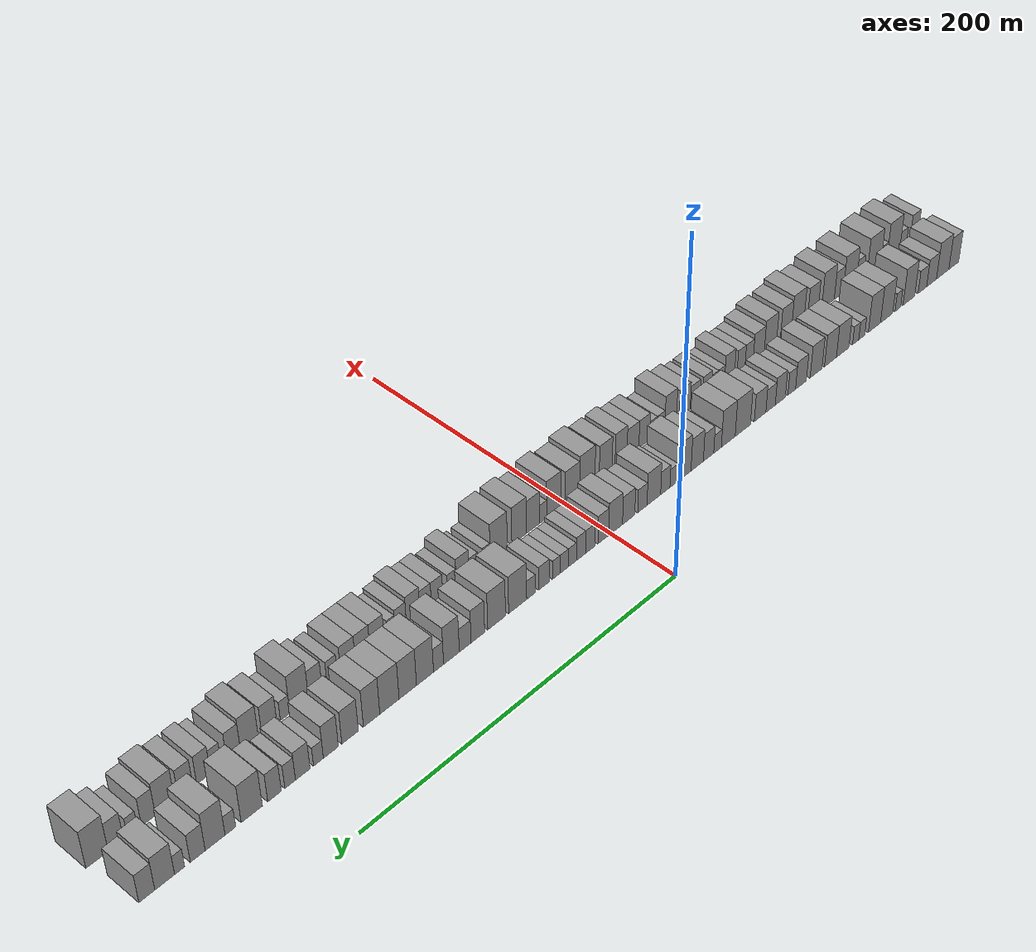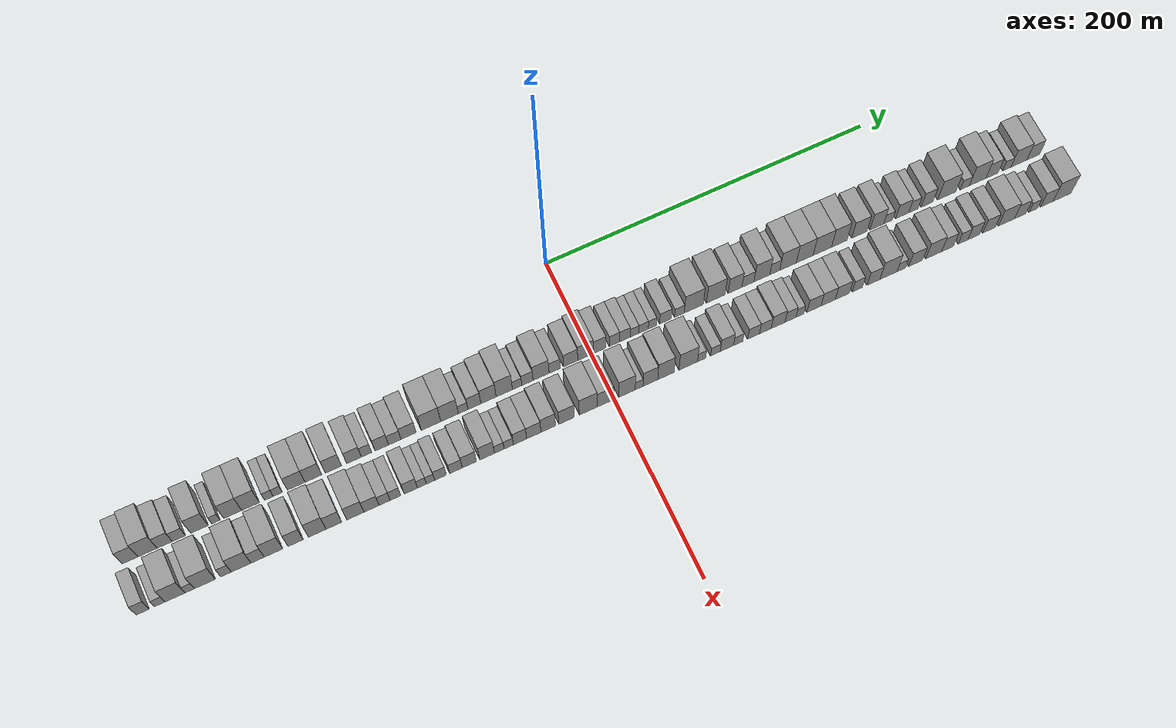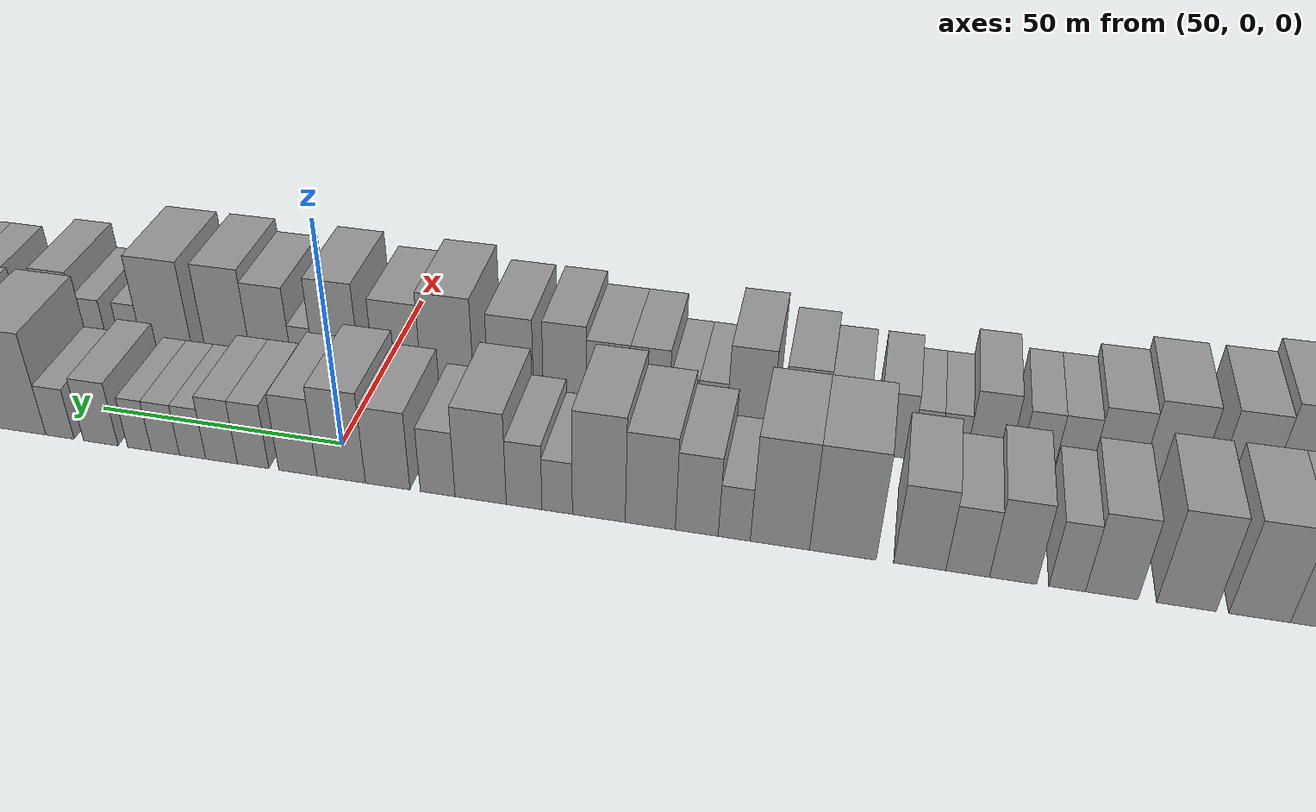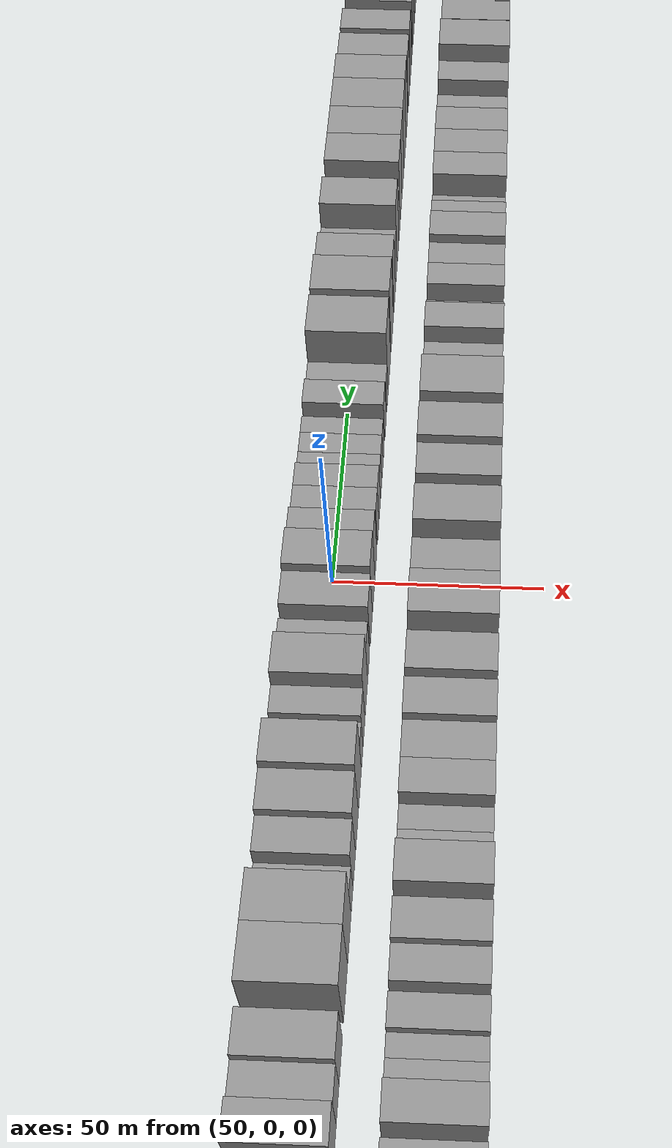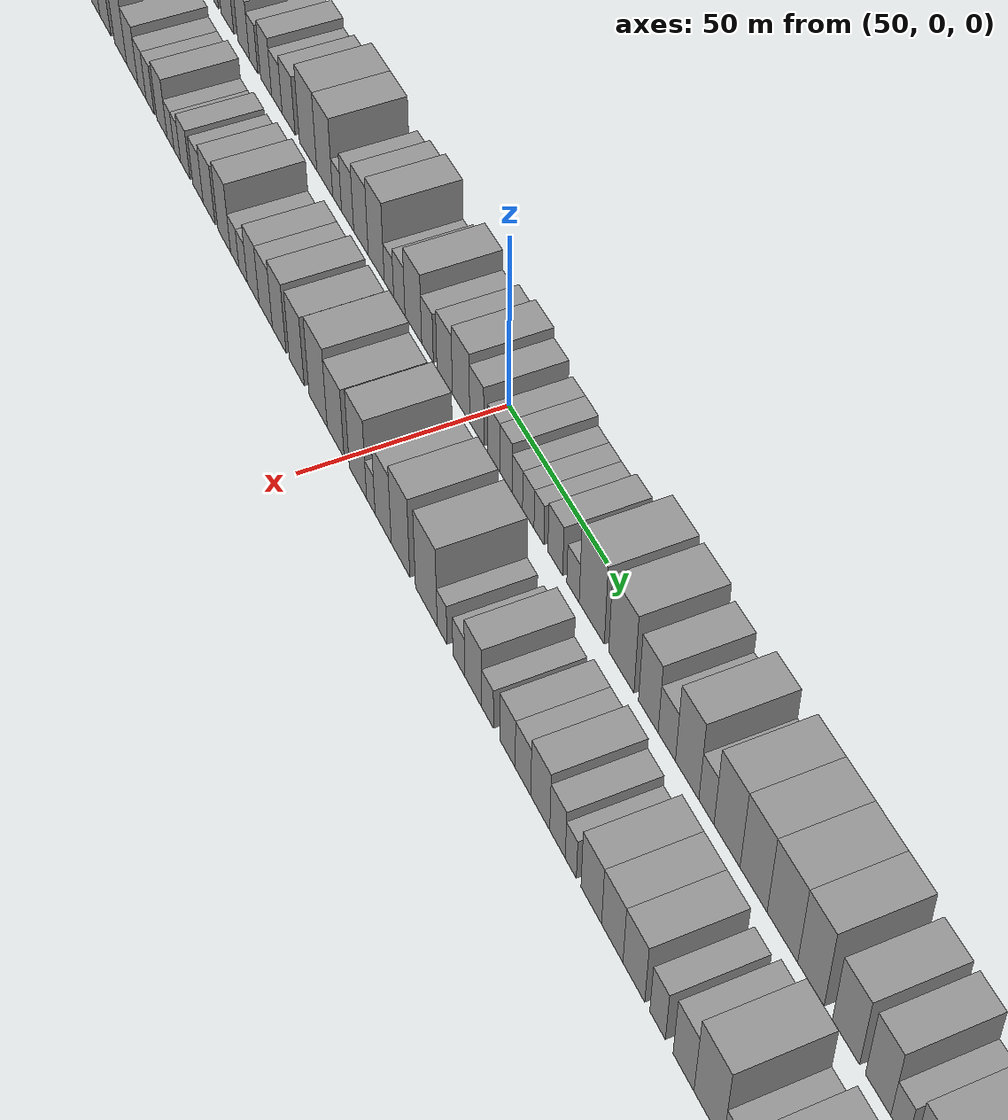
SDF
<sdf version="1.6">
 <world name="default">
  <scene>
   <sky><clouds><speed>12</speed></clouds></sky>
   <ambient>0.4 0.4 0.4 1</ambient>
   <background>0.7 0.7 0.7 1</background>
   <shadows>1</shadows>
  </scene>
  <gravity>0 0 -9.8066</gravity>
  <magnetic_field>6e-06 2.3e-05 -4.2e-05</magnetic_field>
  <physics default="0" name="default_physics" type="ode">
   <ode>
    <solver>
     <type>quick</type>
     <iters>10</iters>
     <sor>1.0</sor>
     <use_dynamic_moi_rescaling>0</use_dynamic_moi_rescaling>
    </solver>
    <constraints>
     <cfm>0</cfm>
     <erp>0.2</erp>
     <contact_max_correcting_vel>100</contact_max_correcting_vel>
     <contact_surface_layer>0.001</contact_surface_layer>
    </constraints>
   </ode>
   <max_step_size>0.004</max_step_size>
   <real_time_factor>1</real_time_factor>
   <real_time_update_rate>250</real_time_update_rate>
  </physics>
  <light name="sun" type="directional">
   <pose>0 0 10 0 0 0</pose>
   <diffuse>0.8 0.8 0.8 1</diffuse>
   <specular>0.2 0.2 0.2 1</specular>
   <attenuation>
    <range>1000</range>
    <constant>0.9</constant>
    <linear>0.01</linear>
    <quadratic>0.001</quadratic>
   </attenuation>
   <direction>-0.5 0.1 -0.9</direction>
  </light>
  <model name="building_1">
   <static>1</static>
   <pose>50.0000 -270.5878 0 0.000000 0.000000 0.000000</pose>
   <link name="link">
    <pose>0 0 10.50 0 0 0</pose>
    <collision name="collision"><geometry><box><size>20.0000 8.8244 21.0000</size></box></geometry></collision>
    <visual name="visual">
     <cast_shadows>0</cast_shadows>
     <geometry><box><size>20.0000 8.8244 21.0000</size></box></geometry>
     <material>
      <script>
       <uri>model://grey_wall/materials/scripts</uri>
       <uri>model://grey_wall/materials/textures</uri>
       <name>vrc/grey_wall</name>
      </script>
     </material>
    </visual>
   </link>
  </model>
  <model name="building_2">
   <static>1</static>
   <pose>50.0000 -260.7174 0 0.000000 0.000000 0.000000</pose>
   <link name="link">
    <pose>0 0 12.00 0 0 0</pose>
    <collision name="collision"><geometry><box><size>20.0000 10.9165 24.0000</size></box></geometry></collision>
    <visual name="visual">
     <cast_shadows>0</cast_shadows>
     <geometry><box><size>20.0000 10.9165 24.0000</size></box></geometry>
     <material>
      <script>
       <uri>model://grey_wall/materials/scripts</uri>
       <uri>model://grey_wall/materials/textures</uri>
       <name>vrc/grey_wall</name>
      </script>
     </material>
    </visual>
   </link>
  </model>
  <model name="building_3">
   <static>1</static>
   <pose>50.0000 -250.9753 0 0.000000 0.000000 0.000000</pose>
   <link name="link">
    <pose>0 0 9.00 0 0 0</pose>
    <collision name="collision"><geometry><box><size>20.0000 8.5676 18.0000</size></box></geometry></collision>
    <visual name="visual">
     <cast_shadows>0</cast_shadows>
     <geometry><box><size>20.0000 8.5676 18.0000</size></box></geometry>
     <material>
      <script>
       <uri>model://grey_wall/materials/scripts</uri>
       <uri>model://grey_wall/materials/textures</uri>
       <name>vrc/grey_wall</name>
      </script>
     </material>
    </visual>
   </link>
  </model>
  <model name="building_4">
   <static>1</static>
   <pose>50.0000 -242.9473 0 0.000000 0.000000 0.000000</pose>
   <link name="link">
    <pose>0 0 7.50 0 0 0</pose>
    <collision name="collision"><geometry><box><size>20.0000 7.4884 15.0000</size></box></geometry></collision>
    <visual name="visual">
     <cast_shadows>0</cast_shadows>
     <geometry><box><size>20.0000 7.4884 15.0000</size></box></geometry>
     <material>
      <script>
       <uri>model://grey_wall/materials/scripts</uri>
       <uri>model://grey_wall/materials/textures</uri>
       <name>vrc/grey_wall</name>
      </script>
     </material>
    </visual>
   </link>
  </model>
  <model name="building_5">
   <static>1</static>
   <pose>50.0000 -231.1971 0 0.000000 0.000000 0.000000</pose>
   <link name="link">
    <pose>0 0 12.00 0 0 0</pose>
    <collision name="collision"><geometry><box><size>20.0000 10.0120 24.0000</size></box></geometry></collision>
    <visual name="visual">
     <cast_shadows>0</cast_shadows>
     <geometry><box><size>20.0000 10.0120 24.0000</size></box></geometry>
     <material>
      <script>
       <uri>model://grey_wall/materials/scripts</uri>
       <uri>model://grey_wall/materials/textures</uri>
       <name>vrc/grey_wall</name>
      </script>
     </material>
    </visual>
   </link>
  </model>
  <model name="building_6">
   <static>1</static>
   <pose>50.0000 -221.7817 0 0.000000 0.000000 0.000000</pose>
   <link name="link">
    <pose>0 0 6.00 0 0 0</pose>
    <collision name="collision"><geometry><box><size>20.0000 4.8187 12.0000</size></box></geometry></collision>
    <visual name="visual">
     <cast_shadows>0</cast_shadows>
     <geometry><box><size>20.0000 4.8187 12.0000</size></box></geometry>
     <material>
      <script>
       <uri>model://grey_wall/materials/scripts</uri>
       <uri>model://grey_wall/materials/textures</uri>
       <name>vrc/grey_wall</name>
      </script>
     </material>
    </visual>
   </link>
  </model>
  <model name="building_7">
   <static>1</static>
   <pose>50.0000 -212.1964 0 0.000000 0.000000 0.000000</pose>
   <link name="link">
    <pose>0 0 12.00 0 0 0</pose>
    <collision name="collision"><geometry><box><size>20.0000 10.3518 24.0000</size></box></geometry></collision>
    <visual name="visual">
     <cast_shadows>0</cast_shadows>
     <geometry><box><size>20.0000 10.3518 24.0000</size></box></geometry>
     <material>
      <script>
       <uri>model://grey_wall/materials/scripts</uri>
       <uri>model://grey_wall/materials/textures</uri>
       <name>vrc/grey_wall</name>
      </script>
     </material>
    </visual>
   </link>
  </model>
  <model name="building_8">
   <static>1</static>
   <pose>50.0000 -201.9319 0 0.000000 0.000000 0.000000</pose>
   <link name="link">
    <pose>0 0 12.00 0 0 0</pose>
    <collision name="collision"><geometry><box><size>20.0000 10.1771 24.0000</size></box></geometry></collision>
    <visual name="visual">
     <cast_shadows>0</cast_shadows>
     <geometry><box><size>20.0000 10.1771 24.0000</size></box></geometry>
     <material>
      <script>
       <uri>model://grey_wall/materials/scripts</uri>
       <uri>model://grey_wall/materials/textures</uri>
       <name>vrc/grey_wall</name>
      </script>
     </material>
    </visual>
   </link>
  </model>
  <model name="building_9">
   <static>1</static>
   <pose>50.0000 -191.3443 0 0.000000 0.000000 0.000000</pose>
   <link name="link">
    <pose>0 0 6.00 0 0 0</pose>
    <collision name="collision"><geometry><box><size>20.0000 4.9982 12.0000</size></box></geometry></collision>
    <visual name="visual">
     <cast_shadows>0</cast_shadows>
     <geometry><box><size>20.0000 4.9982 12.0000</size></box></geometry>
     <material>
      <script>
       <uri>model://grey_wall/materials/scripts</uri>
       <uri>model://grey_wall/materials/textures</uri>
       <name>vrc/grey_wall</name>
      </script>
     </material>
    </visual>
   </link>
  </model>
  <model name="building_10">
   <static>1</static>
   <pose>50.0000 -186.2483 0 0.000000 0.000000 0.000000</pose>
   <link name="link">
    <pose>0 0 6.00 0 0 0</pose>
    <collision name="collision"><geometry><box><size>20.0000 5.1938 12.0000</size></box></geometry></collision>
    <visual name="visual">
     <cast_shadows>0</cast_shadows>
     <geometry><box><size>20.0000 5.1938 12.0000</size></box></geometry>
     <material>
      <script>
       <uri>model://grey_wall/materials/scripts</uri>
       <uri>model://grey_wall/materials/textures</uri>
       <name>vrc/grey_wall</name>
      </script>
     </material>
    </visual>
   </link>
  </model>
  <model name="building_11">
   <static>1</static>
   <pose>50.0000 -175.5425 0 0.000000 0.000000 0.000000</pose>
   <link name="link">
    <pose>0 0 10.50 0 0 0</pose>
    <collision name="collision"><geometry><box><size>20.0000 10.2178 21.0000</size></box></geometry></collision>
    <visual name="visual">
     <cast_shadows>0</cast_shadows>
     <geometry><box><size>20.0000 10.2178 21.0000</size></box></geometry>
     <material>
      <script>
       <uri>model://grey_wall/materials/scripts</uri>
       <uri>model://grey_wall/materials/textures</uri>
       <name>vrc/grey_wall</name>
      </script>
     </material>
    </visual>
   </link>
  </model>
  <model name="building_12">
   <static>1</static>
   <pose>50.0000 -165.5731 0 0.000000 0.000000 0.000000</pose>
   <link name="link">
    <pose>0 0 10.50 0 0 0</pose>
    <collision name="collision"><geometry><box><size>20.0000 9.7209 21.0000</size></box></geometry></collision>
    <visual name="visual">
     <cast_shadows>0</cast_shadows>
     <geometry><box><size>20.0000 9.7209 21.0000</size></box></geometry>
     <material>
      <script>
       <uri>model://grey_wall/materials/scripts</uri>
       <uri>model://grey_wall/materials/textures</uri>
       <name>vrc/grey_wall</name>
      </script>
     </material>
    </visual>
   </link>
  </model>
  <model name="building_13">
   <static>1</static>
   <pose>50.0000 -153.9268 0 0.000000 0.000000 0.000000</pose>
   <link name="link">
    <pose>0 0 10.50 0 0 0</pose>
    <collision name="collision"><geometry><box><size>20.0000 9.5718 21.0000</size></box></geometry></collision>
    <visual name="visual">
     <cast_shadows>0</cast_shadows>
     <geometry><box><size>20.0000 9.5718 21.0000</size></box></geometry>
     <material>
      <script>
       <uri>model://grey_wall/materials/scripts</uri>
       <uri>model://grey_wall/materials/textures</uri>
       <name>vrc/grey_wall</name>
      </script>
     </material>
    </visual>
   </link>
  </model>
  <model name="building_14">
   <static>1</static>
   <pose>50.0000 -141.8351 0 0.000000 0.000000 0.000000</pose>
   <link name="link">
    <pose>0 0 9.00 0 0 0</pose>
    <collision name="collision"><geometry><box><size>20.0000 8.6117 18.0000</size></box></geometry></collision>
    <visual name="visual">
     <cast_shadows>0</cast_shadows>
     <geometry><box><size>20.0000 8.6117 18.0000</size></box></geometry>
     <material>
      <script>
       <uri>model://grey_wall/materials/scripts</uri>
       <uri>model://grey_wall/materials/textures</uri>
       <name>vrc/grey_wall</name>
      </script>
     </material>
    </visual>
   </link>
  </model>
  <model name="building_15">
   <static>1</static>
   <pose>50.0000 -134.5054 0 0.000000 0.000000 0.000000</pose>
   <link name="link">
    <pose>0 0 7.50 0 0 0</pose>
    <collision name="collision"><geometry><box><size>20.0000 6.0475 15.0000</size></box></geometry></collision>
    <visual name="visual">
     <cast_shadows>0</cast_shadows>
     <geometry><box><size>20.0000 6.0475 15.0000</size></box></geometry>
     <material>
      <script>
       <uri>model://grey_wall/materials/scripts</uri>
       <uri>model://grey_wall/materials/textures</uri>
       <name>vrc/grey_wall</name>
      </script>
     </material>
    </visual>
   </link>
  </model>
  <model name="building_16">
   <static>1</static>
   <pose>50.0000 -125.5305 0 0.000000 0.000000 0.000000</pose>
   <link name="link">
    <pose>0 0 9.00 0 0 0</pose>
    <collision name="collision"><geometry><box><size>20.0000 7.9024 18.0000</size></box></geometry></collision>
    <visual name="visual">
     <cast_shadows>0</cast_shadows>
     <geometry><box><size>20.0000 7.9024 18.0000</size></box></geometry>
     <material>
      <script>
       <uri>model://grey_wall/materials/scripts</uri>
       <uri>model://grey_wall/materials/textures</uri>
       <name>vrc/grey_wall</name>
      </script>
     </material>
    </visual>
   </link>
  </model>
  <model name="building_17">
   <static>1</static>
   <pose>50.0000 -117.8935 0 0.000000 0.000000 0.000000</pose>
   <link name="link">
    <pose>0 0 7.50 0 0 0</pose>
    <collision name="collision"><geometry><box><size>20.0000 7.3716 15.0000</size></box></geometry></collision>
    <visual name="visual">
     <cast_shadows>0</cast_shadows>
     <geometry><box><size>20.0000 7.3716 15.0000</size></box></geometry>
     <material>
      <script>
       <uri>model://grey_wall/materials/scripts</uri>
       <uri>model://grey_wall/materials/textures</uri>
       <name>vrc/grey_wall</name>
      </script>
     </material>
    </visual>
   </link>
  </model>
  <model name="building_18">
   <static>1</static>
   <pose>50.0000 -109.7421 0 0.000000 0.000000 0.000000</pose>
   <link name="link">
    <pose>0 0 9.00 0 0 0</pose>
    <collision name="collision"><geometry><box><size>20.0000 8.9311 18.0000</size></box></geometry></collision>
    <visual name="visual">
     <cast_shadows>0</cast_shadows>
     <geometry><box><size>20.0000 8.9311 18.0000</size></box></geometry>
     <material>
      <script>
       <uri>model://grey_wall/materials/scripts</uri>
       <uri>model://grey_wall/materials/textures</uri>
       <name>vrc/grey_wall</name>
      </script>
     </material>
    </visual>
   </link>
  </model>
  <model name="building_19">
   <static>1</static>
   <pose>50.0000 -96.4635 0 0.000000 0.000000 0.000000</pose>
   <link name="link">
    <pose>0 0 12.00 0 0 0</pose>
    <collision name="collision"><geometry><box><size>20.0000 11.6262 24.0000</size></box></geometry></collision>
    <visual name="visual">
     <cast_shadows>0</cast_shadows>
     <geometry><box><size>20.0000 11.6262 24.0000</size></box></geometry>
     <material>
      <script>
       <uri>model://grey_wall/materials/scripts</uri>
       <uri>model://grey_wall/materials/textures</uri>
       <name>vrc/grey_wall</name>
      </script>
     </material>
    </visual>
   </link>
  </model>
  <model name="building_20">
   <static>1</static>
   <pose>50.0000 -85.4118 0 0.000000 0.000000 0.000000</pose>
   <link name="link">
    <pose>0 0 12.00 0 0 0</pose>
    <collision name="collision"><geometry><box><size>20.0000 10.4770 24.0000</size></box></geometry></collision>
    <visual name="visual">
     <cast_shadows>0</cast_shadows>
     <geometry><box><size>20.0000 10.4770 24.0000</size></box></geometry>
     <material>
      <script>
       <uri>model://grey_wall/materials/scripts</uri>
       <uri>model://grey_wall/materials/textures</uri>
       <name>vrc/grey_wall</name>
      </script>
     </material>
    </visual>
   </link>
  </model>
  <model name="building_21">
   <static>1</static>
   <pose>50.0000 -77.3133 0 0.000000 0.000000 0.000000</pose>
   <link name="link">
    <pose>0 0 6.00 0 0 0</pose>
    <collision name="collision"><geometry><box><size>20.0000 5.7202 12.0000</size></box></geometry></collision>
    <visual name="visual">
     <cast_shadows>0</cast_shadows>
     <geometry><box><size>20.0000 5.7202 12.0000</size></box></geometry>
     <material>
      <script>
       <uri>model://grey_wall/materials/scripts</uri>
       <uri>model://grey_wall/materials/textures</uri>
       <name>vrc/grey_wall</name>
      </script>
     </material>
    </visual>
   </link>
  </model>
  <model name="building_22">
   <static>1</static>
   <pose>50.0000 -70.5814 0 0.000000 0.000000 0.000000</pose>
   <link name="link">
    <pose>0 0 9.00 0 0 0</pose>
    <collision name="collision"><geometry><box><size>20.0000 7.7435 18.0000</size></box></geometry></collision>
    <visual name="visual">
     <cast_shadows>0</cast_shadows>
     <geometry><box><size>20.0000 7.7435 18.0000</size></box></geometry>
     <material>
      <script>
       <uri>model://grey_wall/materials/scripts</uri>
       <uri>model://grey_wall/materials/textures</uri>
       <name>vrc/grey_wall</name>
      </script>
     </material>
    </visual>
   </link>
  </model>
  <model name="building_23">
   <static>1</static>
   <pose>50.0000 -62.1440 0 0.000000 0.000000 0.000000</pose>
   <link name="link">
    <pose>0 0 10.50 0 0 0</pose>
    <collision name="collision"><geometry><box><size>20.0000 9.1313 21.0000</size></box></geometry></collision>
    <visual name="visual">
     <cast_shadows>0</cast_shadows>
     <geometry><box><size>20.0000 9.1313 21.0000</size></box></geometry>
     <material>
      <script>
       <uri>model://grey_wall/materials/scripts</uri>
       <uri>model://grey_wall/materials/textures</uri>
       <name>vrc/grey_wall</name>
      </script>
     </material>
    </visual>
   </link>
  </model>
  <model name="building_24">
   <static>1</static>
   <pose>50.0000 -52.6865 0 0.000000 0.000000 0.000000</pose>
   <link name="link">
    <pose>0 0 12.00 0 0 0</pose>
    <collision name="collision"><geometry><box><size>20.0000 9.7836 24.0000</size></box></geometry></collision>
    <visual name="visual">
     <cast_shadows>0</cast_shadows>
     <geometry><box><size>20.0000 9.7836 24.0000</size></box></geometry>
     <material>
      <script>
       <uri>model://grey_wall/materials/scripts</uri>
       <uri>model://grey_wall/materials/textures</uri>
       <name>vrc/grey_wall</name>
      </script>
     </material>
    </visual>
   </link>
  </model>
  <model name="building_25">
   <static>1</static>
   <pose>50.0000 -44.9658 0 0.000000 0.000000 0.000000</pose>
   <link name="link">
    <pose>0 0 6.00 0 0 0</pose>
    <collision name="collision"><geometry><box><size>20.0000 5.6578 12.0000</size></box></geometry></collision>
    <visual name="visual">
     <cast_shadows>0</cast_shadows>
     <geometry><box><size>20.0000 5.6578 12.0000</size></box></geometry>
     <material>
      <script>
       <uri>model://grey_wall/materials/scripts</uri>
       <uri>model://grey_wall/materials/textures</uri>
       <name>vrc/grey_wall</name>
      </script>
     </material>
    </visual>
   </link>
  </model>
  <model name="building_26">
   <static>1</static>
   <pose>50.0000 -38.7752 0 0.000000 0.000000 0.000000</pose>
   <link name="link">
    <pose>0 0 7.50 0 0 0</pose>
    <collision name="collision"><geometry><box><size>20.0000 6.7235 15.0000</size></box></geometry></collision>
    <visual name="visual">
     <cast_shadows>0</cast_shadows>
     <geometry><box><size>20.0000 6.7235 15.0000</size></box></geometry>
     <material>
      <script>
       <uri>model://grey_wall/materials/scripts</uri>
       <uri>model://grey_wall/materials/textures</uri>
       <name>vrc/grey_wall</name>
      </script>
     </material>
    </visual>
   </link>
  </model>
  <model name="building_27">
   <static>1</static>
   <pose>50.0000 -30.5352 0 0.000000 0.000000 0.000000</pose>
   <link name="link">
    <pose>0 0 10.50 0 0 0</pose>
    <collision name="collision"><geometry><box><size>20.0000 9.7567 21.0000</size></box></geometry></collision>
    <visual name="visual">
     <cast_shadows>0</cast_shadows>
     <geometry><box><size>20.0000 9.7567 21.0000</size></box></geometry>
     <material>
      <script>
       <uri>model://grey_wall/materials/scripts</uri>
       <uri>model://grey_wall/materials/textures</uri>
       <name>vrc/grey_wall</name>
      </script>
     </material>
    </visual>
   </link>
  </model>
  <model name="building_28">
   <static>1</static>
   <pose>50.0000 -22.3069 0 0.000000 0.000000 0.000000</pose>
   <link name="link">
    <pose>0 0 7.50 0 0 0</pose>
    <collision name="collision"><geometry><box><size>20.0000 6.6999 15.0000</size></box></geometry></collision>
    <visual name="visual">
     <cast_shadows>0</cast_shadows>
     <geometry><box><size>20.0000 6.6999 15.0000</size></box></geometry>
     <material>
      <script>
       <uri>model://grey_wall/materials/scripts</uri>
       <uri>model://grey_wall/materials/textures</uri>
       <name>vrc/grey_wall</name>
      </script>
     </material>
    </visual>
   </link>
  </model>
  <model name="building_29">
   <static>1</static>
   <pose>50.0000 -12.6182 0 0.000000 0.000000 0.000000</pose>
   <link name="link">
    <pose>0 0 9.00 0 0 0</pose>
    <collision name="collision"><geometry><box><size>20.0000 8.6775 18.0000</size></box></geometry></collision>
    <visual name="visual">
     <cast_shadows>0</cast_shadows>
     <geometry><box><size>20.0000 8.6775 18.0000</size></box></geometry>
     <material>
      <script>
       <uri>model://grey_wall/materials/scripts</uri>
       <uri>model://grey_wall/materials/textures</uri>
       <name>vrc/grey_wall</name>
      </script>
     </material>
    </visual>
   </link>
  </model>
  <model name="building_30">
   <static>1</static>
   <pose>50.0000 -3.4968 0 0.000000 0.000000 0.000000</pose>
   <link name="link">
    <pose>0 0 10.50 0 0 0</pose>
    <collision name="collision"><geometry><box><size>20.0000 9.5653 21.0000</size></box></geometry></collision>
    <visual name="visual">
     <cast_shadows>0</cast_shadows>
     <geometry><box><size>20.0000 9.5653 21.0000</size></box></geometry>
     <material>
      <script>
       <uri>model://grey_wall/materials/scripts</uri>
       <uri>model://grey_wall/materials/textures</uri>
       <name>vrc/grey_wall</name>
      </script>
     </material>
    </visual>
   </link>
  </model>
  <model name="building_31">
   <static>1</static>
   <pose>50.0000 5.1058 0 0.000000 0.000000 0.000000</pose>
   <link name="link">
    <pose>0 0 9.00 0 0 0</pose>
    <collision name="collision"><geometry><box><size>20.0000 7.6399 18.0000</size></box></geometry></collision>
    <visual name="visual">
     <cast_shadows>0</cast_shadows>
     <geometry><box><size>20.0000 7.6399 18.0000</size></box></geometry>
     <material>
      <script>
       <uri>model://grey_wall/materials/scripts</uri>
       <uri>model://grey_wall/materials/textures</uri>
       <name>vrc/grey_wall</name>
      </script>
     </material>
    </visual>
   </link>
  </model>
  <model name="building_32">
   <static>1</static>
   <pose>50.0000 14.0946 0 0.000000 0.000000 0.000000</pose>
   <link name="link">
    <pose>0 0 7.50 0 0 0</pose>
    <collision name="collision"><geometry><box><size>20.0000 6.3376 15.0000</size></box></geometry></collision>
    <visual name="visual">
     <cast_shadows>0</cast_shadows>
     <geometry><box><size>20.0000 6.3376 15.0000</size></box></geometry>
     <material>
      <script>
       <uri>model://grey_wall/materials/scripts</uri>
       <uri>model://grey_wall/materials/textures</uri>
       <name>vrc/grey_wall</name>
      </script>
     </material>
    </visual>
   </link>
  </model>
  <model name="building_33">
   <static>1</static>
   <pose>50.0000 20.4826 0 0.000000 0.000000 0.000000</pose>
   <link name="link">
    <pose>0 0 7.50 0 0 0</pose>
    <collision name="collision"><geometry><box><size>20.0000 6.4384 15.0000</size></box></geometry></collision>
    <visual name="visual">
     <cast_shadows>0</cast_shadows>
     <geometry><box><size>20.0000 6.4384 15.0000</size></box></geometry>
     <material>
      <script>
       <uri>model://grey_wall/materials/scripts</uri>
       <uri>model://grey_wall/materials/textures</uri>
       <name>vrc/grey_wall</name>
      </script>
     </material>
    </visual>
   </link>
  </model>
  <model name="building_34">
   <static>1</static>
   <pose>50.0000 26.3966 0 0.000000 0.000000 0.000000</pose>
   <link name="link">
    <pose>0 0 6.00 0 0 0</pose>
    <collision name="collision"><geometry><box><size>20.0000 5.3897 12.0000</size></box></geometry></collision>
    <visual name="visual">
     <cast_shadows>0</cast_shadows>
     <geometry><box><size>20.0000 5.3897 12.0000</size></box></geometry>
     <material>
      <script>
       <uri>model://grey_wall/materials/scripts</uri>
       <uri>model://grey_wall/materials/textures</uri>
       <name>vrc/grey_wall</name>
      </script>
     </material>
    </visual>
   </link>
  </model>
  <model name="building_35">
   <static>1</static>
   <pose>50.0000 32.0013 0 0.000000 0.000000 0.000000</pose>
   <link name="link">
    <pose>0 0 6.00 0 0 0</pose>
    <collision name="collision"><geometry><box><size>20.0000 5.8198 12.0000</size></box></geometry></collision>
    <visual name="visual">
     <cast_shadows>0</cast_shadows>
     <geometry><box><size>20.0000 5.8198 12.0000</size></box></geometry>
     <material>
      <script>
       <uri>model://grey_wall/materials/scripts</uri>
       <uri>model://grey_wall/materials/textures</uri>
       <name>vrc/grey_wall</name>
      </script>
     </material>
    </visual>
   </link>
  </model>
  <model name="building_36">
   <static>1</static>
   <pose>50.0000 37.3759 0 0.000000 0.000000 0.000000</pose>
   <link name="link">
    <pose>0 0 6.00 0 0 0</pose>
    <collision name="collision"><geometry><box><size>20.0000 4.9294 12.0000</size></box></geometry></collision>
    <visual name="visual">
     <cast_shadows>0</cast_shadows>
     <geometry><box><size>20.0000 4.9294 12.0000</size></box></geometry>
     <material>
      <script>
       <uri>model://grey_wall/materials/scripts</uri>
       <uri>model://grey_wall/materials/textures</uri>
       <name>vrc/grey_wall</name>
      </script>
     </material>
    </visual>
   </link>
  </model>
  <model name="building_37">
   <static>1</static>
   <pose>50.0000 45.4599 0 0.000000 0.000000 0.000000</pose>
   <link name="link">
    <pose>0 0 7.50 0 0 0</pose>
    <collision name="collision"><geometry><box><size>20.0000 7.2387 15.0000</size></box></geometry></collision>
    <visual name="visual">
     <cast_shadows>0</cast_shadows>
     <geometry><box><size>20.0000 7.2387 15.0000</size></box></geometry>
     <material>
      <script>
       <uri>model://grey_wall/materials/scripts</uri>
       <uri>model://grey_wall/materials/textures</uri>
       <name>vrc/grey_wall</name>
      </script>
     </material>
    </visual>
   </link>
  </model>
  <model name="building_38">
   <static>1</static>
   <pose>50.0000 54.0677 0 0.000000 0.000000 0.000000</pose>
   <link name="link">
    <pose>0 0 6.00 0 0 0</pose>
    <collision name="collision"><geometry><box><size>20.0000 5.9769 12.0000</size></box></geometry></collision>
    <visual name="visual">
     <cast_shadows>0</cast_shadows>
     <geometry><box><size>20.0000 5.9769 12.0000</size></box></geometry>
     <material>
      <script>
       <uri>model://grey_wall/materials/scripts</uri>
       <uri>model://grey_wall/materials/textures</uri>
       <name>vrc/grey_wall</name>
      </script>
     </material>
    </visual>
   </link>
  </model>
  <model name="building_39">
   <static>1</static>
   <pose>50.0000 62.9731 0 0.000000 0.000000 0.000000</pose>
   <link name="link">
    <pose>0 0 12.00 0 0 0</pose>
    <collision name="collision"><geometry><box><size>20.0000 11.8338 24.0000</size></box></geometry></collision>
    <visual name="visual">
     <cast_shadows>0</cast_shadows>
     <geometry><box><size>20.0000 11.8338 24.0000</size></box></geometry>
     <material>
      <script>
       <uri>model://grey_wall/materials/scripts</uri>
       <uri>model://grey_wall/materials/textures</uri>
       <name>vrc/grey_wall</name>
      </script>
     </material>
    </visual>
   </link>
  </model>
  <model name="building_40">
   <static>1</static>
   <pose>50.0000 76.6518 0 0.000000 0.000000 0.000000</pose>
   <link name="link">
    <pose>0 0 12.00 0 0 0</pose>
    <collision name="collision"><geometry><box><size>20.0000 11.5236 24.0000</size></box></geometry></collision>
    <visual name="visual">
     <cast_shadows>0</cast_shadows>
     <geometry><box><size>20.0000 11.5236 24.0000</size></box></geometry>
     <material>
      <script>
       <uri>model://grey_wall/materials/scripts</uri>
       <uri>model://grey_wall/materials/textures</uri>
       <name>vrc/grey_wall</name>
      </script>
     </material>
    </visual>
   </link>
  </model>
  <model name="building_41">
   <static>1</static>
   <pose>50.0000 88.7374 0 0.000000 0.000000 0.000000</pose>
   <link name="link">
    <pose>0 0 10.50 0 0 0</pose>
    <collision name="collision"><geometry><box><size>20.0000 8.6478 21.0000</size></box></geometry></collision>
    <visual name="visual">
     <cast_shadows>0</cast_shadows>
     <geometry><box><size>20.0000 8.6478 21.0000</size></box></geometry>
     <material>
      <script>
       <uri>model://grey_wall/materials/scripts</uri>
       <uri>model://grey_wall/materials/textures</uri>
       <name>vrc/grey_wall</name>
      </script>
     </material>
    </visual>
   </link>
  </model>
  <model name="building_42">
   <static>1</static>
   <pose>50.0000 96.8097 0 0.000000 0.000000 0.000000</pose>
   <link name="link">
    <pose>0 0 7.50 0 0 0</pose>
    <collision name="collision"><geometry><box><size>20.0000 7.4968 15.0000</size></box></geometry></collision>
    <visual name="visual">
     <cast_shadows>0</cast_shadows>
     <geometry><box><size>20.0000 7.4968 15.0000</size></box></geometry>
     <material>
      <script>
       <uri>model://grey_wall/materials/scripts</uri>
       <uri>model://grey_wall/materials/textures</uri>
       <name>vrc/grey_wall</name>
      </script>
     </material>
    </visual>
   </link>
  </model>
  <model name="building_43">
   <static>1</static>
   <pose>50.0000 105.5045 0 0.000000 0.000000 0.000000</pose>
   <link name="link">
    <pose>0 0 12.00 0 0 0</pose>
    <collision name="collision"><geometry><box><size>20.0000 9.8928 24.0000</size></box></geometry></collision>
    <visual name="visual">
     <cast_shadows>0</cast_shadows>
     <geometry><box><size>20.0000 9.8928 24.0000</size></box></geometry>
     <material>
      <script>
       <uri>model://grey_wall/materials/scripts</uri>
       <uri>model://grey_wall/materials/textures</uri>
       <name>vrc/grey_wall</name>
      </script>
     </material>
    </visual>
   </link>
  </model>
  <model name="building_44">
   <static>1</static>
   <pose>50.0000 113.5807 0 0.000000 0.000000 0.000000</pose>
   <link name="link">
    <pose>0 0 7.50 0 0 0</pose>
    <collision name="collision"><geometry><box><size>20.0000 6.2596 15.0000</size></box></geometry></collision>
    <visual name="visual">
     <cast_shadows>0</cast_shadows>
     <geometry><box><size>20.0000 6.2596 15.0000</size></box></geometry>
     <material>
      <script>
       <uri>model://grey_wall/materials/scripts</uri>
       <uri>model://grey_wall/materials/textures</uri>
       <name>vrc/grey_wall</name>
      </script>
     </material>
    </visual>
   </link>
  </model>
  <model name="building_45">
   <static>1</static>
   <pose>50.0000 121.9848 0 0.000000 0.000000 0.000000</pose>
   <link name="link">
    <pose>0 0 12.00 0 0 0</pose>
    <collision name="collision"><geometry><box><size>20.0000 10.5485 24.0000</size></box></geometry></collision>
    <visual name="visual">
     <cast_shadows>0</cast_shadows>
     <geometry><box><size>20.0000 10.5485 24.0000</size></box></geometry>
     <material>
      <script>
       <uri>model://grey_wall/materials/scripts</uri>
       <uri>model://grey_wall/materials/textures</uri>
       <name>vrc/grey_wall</name>
      </script>
     </material>
    </visual>
   </link>
  </model>
  <model name="building_46">
   <static>1</static>
   <pose>50.0000 132.5934 0 0.000000 0.000000 0.000000</pose>
   <link name="link">
    <pose>0 0 12.00 0 0 0</pose>
    <collision name="collision"><geometry><box><size>20.0000 10.6686 24.0000</size></box></geometry></collision>
    <visual name="visual">
     <cast_shadows>0</cast_shadows>
     <geometry><box><size>20.0000 10.6686 24.0000</size></box></geometry>
     <material>
      <script>
       <uri>model://grey_wall/materials/scripts</uri>
       <uri>model://grey_wall/materials/textures</uri>
       <name>vrc/grey_wall</name>
      </script>
     </material>
    </visual>
   </link>
  </model>
  <model name="building_47">
   <static>1</static>
   <pose>50.0000 143.7579 0 0.000000 0.000000 0.000000</pose>
   <link name="link">
    <pose>0 0 12.00 0 0 0</pose>
    <collision name="collision"><geometry><box><size>20.0000 11.6604 24.0000</size></box></geometry></collision>
    <visual name="visual">
     <cast_shadows>0</cast_shadows>
     <geometry><box><size>20.0000 11.6604 24.0000</size></box></geometry>
     <material>
      <script>
       <uri>model://grey_wall/materials/scripts</uri>
       <uri>model://grey_wall/materials/textures</uri>
       <name>vrc/grey_wall</name>
      </script>
     </material>
    </visual>
   </link>
  </model>
  <model name="building_48">
   <static>1</static>
   <pose>50.0000 154.5104 0 0.000000 0.000000 0.000000</pose>
   <link name="link">
    <pose>0 0 12.00 0 0 0</pose>
    <collision name="collision"><geometry><box><size>20.0000 9.8446 24.0000</size></box></geometry></collision>
    <visual name="visual">
     <cast_shadows>0</cast_shadows>
     <geometry><box><size>20.0000 9.8446 24.0000</size></box></geometry>
     <material>
      <script>
       <uri>model://grey_wall/materials/scripts</uri>
       <uri>model://grey_wall/materials/textures</uri>
       <name>vrc/grey_wall</name>
      </script>
     </material>
    </visual>
   </link>
  </model>
  <model name="building_49">
   <static>1</static>
   <pose>50.0000 167.3071 0 0.000000 0.000000 0.000000</pose>
   <link name="link">
    <pose>0 0 10.50 0 0 0</pose>
    <collision name="collision"><geometry><box><size>20.0000 9.7488 21.0000</size></box></geometry></collision>
    <visual name="visual">
     <cast_shadows>0</cast_shadows>
     <geometry><box><size>20.0000 9.7488 21.0000</size></box></geometry>
     <material>
      <script>
       <uri>model://grey_wall/materials/scripts</uri>
       <uri>model://grey_wall/materials/textures</uri>
       <name>vrc/grey_wall</name>
      </script>
     </material>
    </visual>
   </link>
  </model>
  <model name="building_50">
   <static>1</static>
   <pose>50.0000 178.5694 0 0.000000 0.000000 0.000000</pose>
   <link name="link">
    <pose>0 0 10.50 0 0 0</pose>
    <collision name="collision"><geometry><box><size>20.0000 8.7759 21.0000</size></box></geometry></collision>
    <visual name="visual">
     <cast_shadows>0</cast_shadows>
     <geometry><box><size>20.0000 8.7759 21.0000</size></box></geometry>
     <material>
      <script>
       <uri>model://grey_wall/materials/scripts</uri>
       <uri>model://grey_wall/materials/textures</uri>
       <name>vrc/grey_wall</name>
      </script>
     </material>
    </visual>
   </link>
  </model>
  <model name="building_51">
   <static>1</static>
   <pose>50.0000 185.8129 0 0.000000 0.000000 0.000000</pose>
   <link name="link">
    <pose>0 0 6.00 0 0 0</pose>
    <collision name="collision"><geometry><box><size>20.0000 5.7110 12.0000</size></box></geometry></collision>
    <visual name="visual">
     <cast_shadows>0</cast_shadows>
     <geometry><box><size>20.0000 5.7110 12.0000</size></box></geometry>
     <material>
      <script>
       <uri>model://grey_wall/materials/scripts</uri>
       <uri>model://grey_wall/materials/textures</uri>
       <name>vrc/grey_wall</name>
      </script>
     </material>
    </visual>
   </link>
  </model>
  <model name="building_52">
   <static>1</static>
   <pose>50.0000 194.8504 0 0.000000 0.000000 0.000000</pose>
   <link name="link">
    <pose>0 0 9.00 0 0 0</pose>
    <collision name="collision"><geometry><box><size>20.0000 8.3639 18.0000</size></box></geometry></collision>
    <visual name="visual">
     <cast_shadows>0</cast_shadows>
     <geometry><box><size>20.0000 8.3639 18.0000</size></box></geometry>
     <material>
      <script>
       <uri>model://grey_wall/materials/scripts</uri>
       <uri>model://grey_wall/materials/textures</uri>
       <name>vrc/grey_wall</name>
      </script>
     </material>
    </visual>
   </link>
  </model>
  <model name="building_53">
   <static>1</static>
   <pose>50.0000 202.0551 0 0.000000 0.000000 0.000000</pose>
   <link name="link">
    <pose>0 0 7.50 0 0 0</pose>
    <collision name="collision"><geometry><box><size>20.0000 6.0456 15.0000</size></box></geometry></collision>
    <visual name="visual">
     <cast_shadows>0</cast_shadows>
     <geometry><box><size>20.0000 6.0456 15.0000</size></box></geometry>
     <material>
      <script>
       <uri>model://grey_wall/materials/scripts</uri>
       <uri>model://grey_wall/materials/textures</uri>
       <name>vrc/grey_wall</name>
      </script>
     </material>
    </visual>
   </link>
  </model>
  <model name="building_54">
   <static>1</static>
   <pose>50.0000 210.8875 0 0.000000 0.000000 0.000000</pose>
   <link name="link">
    <pose>0 0 9.00 0 0 0</pose>
    <collision name="collision"><geometry><box><size>20.0000 7.6192 18.0000</size></box></geometry></collision>
    <visual name="visual">
     <cast_shadows>0</cast_shadows>
     <geometry><box><size>20.0000 7.6192 18.0000</size></box></geometry>
     <material>
      <script>
       <uri>model://grey_wall/materials/scripts</uri>
       <uri>model://grey_wall/materials/textures</uri>
       <name>vrc/grey_wall</name>
      </script>
     </material>
    </visual>
   </link>
  </model>
  <model name="building_55">
   <static>1</static>
   <pose>50.0000 223.5982 0 0.000000 0.000000 0.000000</pose>
   <link name="link">
    <pose>0 0 12.00 0 0 0</pose>
    <collision name="collision"><geometry><box><size>20.0000 11.8020 24.0000</size></box></geometry></collision>
    <visual name="visual">
     <cast_shadows>0</cast_shadows>
     <geometry><box><size>20.0000 11.8020 24.0000</size></box></geometry>
     <material>
      <script>
       <uri>model://grey_wall/materials/scripts</uri>
       <uri>model://grey_wall/materials/textures</uri>
       <name>vrc/grey_wall</name>
      </script>
     </material>
    </visual>
   </link>
  </model>
  <model name="building_56">
   <static>1</static>
   <pose>50.0000 235.4313 0 0.000000 0.000000 0.000000</pose>
   <link name="link">
    <pose>0 0 6.00 0 0 0</pose>
    <collision name="collision"><geometry><box><size>20.0000 5.8642 12.0000</size></box></geometry></collision>
    <visual name="visual">
     <cast_shadows>0</cast_shadows>
     <geometry><box><size>20.0000 5.8642 12.0000</size></box></geometry>
     <material>
      <script>
       <uri>model://grey_wall/materials/scripts</uri>
       <uri>model://grey_wall/materials/textures</uri>
       <name>vrc/grey_wall</name>
      </script>
     </material>
    </visual>
   </link>
  </model>
  <model name="building_57">
   <static>1</static>
   <pose>50.0000 243.7569 0 0.000000 0.000000 0.000000</pose>
   <link name="link">
    <pose>0 0 12.00 0 0 0</pose>
    <collision name="collision"><geometry><box><size>20.0000 10.7869 24.0000</size></box></geometry></collision>
    <visual name="visual">
     <cast_shadows>0</cast_shadows>
     <geometry><box><size>20.0000 10.7869 24.0000</size></box></geometry>
     <material>
      <script>
       <uri>model://grey_wall/materials/scripts</uri>
       <uri>model://grey_wall/materials/textures</uri>
       <name>vrc/grey_wall</name>
      </script>
     </material>
    </visual>
   </link>
  </model>
  <model name="building_58">
   <static>1</static>
   <pose>50.0000 253.1843 0 0.000000 0.000000 0.000000</pose>
   <link name="link">
    <pose>0 0 9.00 0 0 0</pose>
    <collision name="collision"><geometry><box><size>20.0000 8.0679 18.0000</size></box></geometry></collision>
    <visual name="visual">
     <cast_shadows>0</cast_shadows>
     <geometry><box><size>20.0000 8.0679 18.0000</size></box></geometry>
     <material>
      <script>
       <uri>model://grey_wall/materials/scripts</uri>
       <uri>model://grey_wall/materials/textures</uri>
       <name>vrc/grey_wall</name>
      </script>
     </material>
    </visual>
   </link>
  </model>
  <model name="building_59">
   <static>1</static>
   <pose>50.0000 262.8933 0 0.000000 0.000000 0.000000</pose>
   <link name="link">
    <pose>0 0 6.00 0 0 0</pose>
    <collision name="collision"><geometry><box><size>20.0000 5.3500 12.0000</size></box></geometry></collision>
    <visual name="visual">
     <cast_shadows>0</cast_shadows>
     <geometry><box><size>20.0000 5.3500 12.0000</size></box></geometry>
     <material>
      <script>
       <uri>model://grey_wall/materials/scripts</uri>
       <uri>model://grey_wall/materials/textures</uri>
       <name>vrc/grey_wall</name>
      </script>
     </material>
    </visual>
   </link>
  </model>
  <model name="building_60">
   <static>1</static>
   <pose>50.0000 270.7941 0 0.000000 0.000000 0.000000</pose>
   <link name="link">
    <pose>0 0 10.50 0 0 0</pose>
    <collision name="collision"><geometry><box><size>20.0000 10.4516 21.0000</size></box></geometry></collision>
    <visual name="visual">
     <cast_shadows>0</cast_shadows>
     <geometry><box><size>20.0000 10.4516 21.0000</size></box></geometry>
     <material>
      <script>
       <uri>model://grey_wall/materials/scripts</uri>
       <uri>model://grey_wall/materials/textures</uri>
       <name>vrc/grey_wall</name>
      </script>
     </material>
    </visual>
   </link>
  </model>
  <model name="building_61">
   <static>1</static>
   <pose>50.0000 280.1998 0 0.000000 0.000000 0.000000</pose>
   <link name="link">
    <pose>0 0 9.00 0 0 0</pose>
    <collision name="collision"><geometry><box><size>20.0000 8.3598 18.0000</size></box></geometry></collision>
    <visual name="visual">
     <cast_shadows>0</cast_shadows>
     <geometry><box><size>20.0000 8.3598 18.0000</size></box></geometry>
     <material>
      <script>
       <uri>model://grey_wall/materials/scripts</uri>
       <uri>model://grey_wall/materials/textures</uri>
       <name>vrc/grey_wall</name>
      </script>
     </material>
    </visual>
   </link>
  </model>
  <model name="building_62">
   <static>1</static>
   <pose>79.0000 -274.3850 0 0.000000 0.000000 0.000000</pose>
   <link name="link">
    <pose>0 0 9.00 0 0 0</pose>
    <collision name="collision"><geometry><box><size>20.0000 7.2299 18.0000</size></box></geometry></collision>
    <visual name="visual">
     <cast_shadows>0</cast_shadows>
     <geometry><box><size>20.0000 7.2299 18.0000</size></box></geometry>
     <material>
      <script>
       <uri>model://grey_wall/materials/scripts</uri>
       <uri>model://grey_wall/materials/textures</uri>
       <name>vrc/grey_wall</name>
      </script>
     </material>
    </visual>
   </link>
  </model>
  <model name="building_63">
   <static>1</static>
   <pose>79.0000 -264.8488 0 0.000000 0.000000 0.000000</pose>
   <link name="link">
    <pose>0 0 6.00 0 0 0</pose>
    <collision name="collision"><geometry><box><size>20.0000 5.8426 12.0000</size></box></geometry></collision>
    <visual name="visual">
     <cast_shadows>0</cast_shadows>
     <geometry><box><size>20.0000 5.8426 12.0000</size></box></geometry>
     <material>
      <script>
       <uri>model://grey_wall/materials/scripts</uri>
       <uri>model://grey_wall/materials/textures</uri>
       <name>vrc/grey_wall</name>
      </script>
     </material>
    </visual>
   </link>
  </model>
  <model name="building_64">
   <static>1</static>
   <pose>79.0000 -256.2770 0 0.000000 0.000000 0.000000</pose>
   <link name="link">
    <pose>0 0 12.00 0 0 0</pose>
    <collision name="collision"><geometry><box><size>20.0000 11.3010 24.0000</size></box></geometry></collision>
    <visual name="visual">
     <cast_shadows>0</cast_shadows>
     <geometry><box><size>20.0000 11.3010 24.0000</size></box></geometry>
     <material>
      <script>
       <uri>model://grey_wall/materials/scripts</uri>
       <uri>model://grey_wall/materials/textures</uri>
       <name>vrc/grey_wall</name>
      </script>
     </material>
    </visual>
   </link>
  </model>
  <model name="building_65">
   <static>1</static>
   <pose>79.0000 -247.9805 0 0.000000 0.000000 0.000000</pose>
   <link name="link">
    <pose>0 0 6.00 0 0 0</pose>
    <collision name="collision"><geometry><box><size>20.0000 5.2920 12.0000</size></box></geometry></collision>
    <visual name="visual">
     <cast_shadows>0</cast_shadows>
     <geometry><box><size>20.0000 5.2920 12.0000</size></box></geometry>
     <material>
      <script>
       <uri>model://grey_wall/materials/scripts</uri>
       <uri>model://grey_wall/materials/textures</uri>
       <name>vrc/grey_wall</name>
      </script>
     </material>
    </visual>
   </link>
  </model>
  <model name="building_66">
   <static>1</static>
   <pose>79.0000 -239.3951 0 0.000000 0.000000 0.000000</pose>
   <link name="link">
    <pose>0 0 12.00 0 0 0</pose>
    <collision name="collision"><geometry><box><size>20.0000 11.8787 24.0000</size></box></geometry></collision>
    <visual name="visual">
     <cast_shadows>0</cast_shadows>
     <geometry><box><size>20.0000 11.8787 24.0000</size></box></geometry>
     <material>
      <script>
       <uri>model://grey_wall/materials/scripts</uri>
       <uri>model://grey_wall/materials/textures</uri>
       <name>vrc/grey_wall</name>
      </script>
     </material>
    </visual>
   </link>
  </model>
  <model name="building_67">
   <static>1</static>
   <pose>79.0000 -227.4109 0 0.000000 0.000000 0.000000</pose>
   <link name="link">
    <pose>0 0 7.50 0 0 0</pose>
    <collision name="collision"><geometry><box><size>20.0000 6.0897 15.0000</size></box></geometry></collision>
    <visual name="visual">
     <cast_shadows>0</cast_shadows>
     <geometry><box><size>20.0000 6.0897 15.0000</size></box></geometry>
     <material>
      <script>
       <uri>model://grey_wall/materials/scripts</uri>
       <uri>model://grey_wall/materials/textures</uri>
       <name>vrc/grey_wall</name>
      </script>
     </material>
    </visual>
   </link>
  </model>
  <model name="building_68">
   <static>1</static>
   <pose>79.0000 -218.7669 0 0.000000 0.000000 0.000000</pose>
   <link name="link">
    <pose>0 0 12.00 0 0 0</pose>
    <collision name="collision"><geometry><box><size>20.0000 11.1985 24.0000</size></box></geometry></collision>
    <visual name="visual">
     <cast_shadows>0</cast_shadows>
     <geometry><box><size>20.0000 11.1985 24.0000</size></box></geometry>
     <material>
      <script>
       <uri>model://grey_wall/materials/scripts</uri>
       <uri>model://grey_wall/materials/textures</uri>
       <name>vrc/grey_wall</name>
      </script>
     </material>
    </visual>
   </link>
  </model>
  <model name="building_69">
   <static>1</static>
   <pose>79.0000 -209.3993 0 0.000000 0.000000 0.000000</pose>
   <link name="link">
    <pose>0 0 9.00 0 0 0</pose>
    <collision name="collision"><geometry><box><size>20.0000 7.5368 18.0000</size></box></geometry></collision>
    <visual name="visual">
     <cast_shadows>0</cast_shadows>
     <geometry><box><size>20.0000 7.5368 18.0000</size></box></geometry>
     <material>
      <script>
       <uri>model://grey_wall/materials/scripts</uri>
       <uri>model://grey_wall/materials/textures</uri>
       <name>vrc/grey_wall</name>
      </script>
     </material>
    </visual>
   </link>
  </model>
  <model name="building_70">
   <static>1</static>
   <pose>79.0000 -200.3698 0 0.000000 0.000000 0.000000</pose>
   <link name="link">
    <pose>0 0 12.00 0 0 0</pose>
    <collision name="collision"><geometry><box><size>20.0000 10.5223 24.0000</size></box></geometry></collision>
    <visual name="visual">
     <cast_shadows>0</cast_shadows>
     <geometry><box><size>20.0000 10.5223 24.0000</size></box></geometry>
     <material>
      <script>
       <uri>model://grey_wall/materials/scripts</uri>
       <uri>model://grey_wall/materials/textures</uri>
       <name>vrc/grey_wall</name>
      </script>
     </material>
    </visual>
   </link>
  </model>
  <model name="building_71">
   <static>1</static>
   <pose>79.0000 -187.7248 0 0.000000 0.000000 0.000000</pose>
   <link name="link">
    <pose>0 0 10.50 0 0 0</pose>
    <collision name="collision"><geometry><box><size>20.0000 8.7676 21.0000</size></box></geometry></collision>
    <visual name="visual">
     <cast_shadows>0</cast_shadows>
     <geometry><box><size>20.0000 8.7676 21.0000</size></box></geometry>
     <material>
      <script>
       <uri>model://grey_wall/materials/scripts</uri>
       <uri>model://grey_wall/materials/textures</uri>
       <name>vrc/grey_wall</name>
      </script>
     </material>
    </visual>
   </link>
  </model>
  <model name="building_72">
   <static>1</static>
   <pose>79.0000 -175.2675 0 0.000000 0.000000 0.000000</pose>
   <link name="link">
    <pose>0 0 12.00 0 0 0</pose>
    <collision name="collision"><geometry><box><size>20.0000 10.1471 24.0000</size></box></geometry></collision>
    <visual name="visual">
     <cast_shadows>0</cast_shadows>
     <geometry><box><size>20.0000 10.1471 24.0000</size></box></geometry>
     <material>
      <script>
       <uri>model://grey_wall/materials/scripts</uri>
       <uri>model://grey_wall/materials/textures</uri>
       <name>vrc/grey_wall</name>
      </script>
     </material>
    </visual>
   </link>
  </model>
  <model name="building_73">
   <static>1</static>
   <pose>79.0000 -165.6837 0 0.000000 0.000000 0.000000</pose>
   <link name="link">
    <pose>0 0 10.50 0 0 0</pose>
    <collision name="collision"><geometry><box><size>20.0000 9.0206 21.0000</size></box></geometry></collision>
    <visual name="visual">
     <cast_shadows>0</cast_shadows>
     <geometry><box><size>20.0000 9.0206 21.0000</size></box></geometry>
     <material>
      <script>
       <uri>model://grey_wall/materials/scripts</uri>
       <uri>model://grey_wall/materials/textures</uri>
       <name>vrc/grey_wall</name>
      </script>
     </material>
    </visual>
   </link>
  </model>
  <model name="building_74">
   <static>1</static>
   <pose>79.0000 -153.2430 0 0.000000 0.000000 0.000000</pose>
   <link name="link">
    <pose>0 0 10.50 0 0 0</pose>
    <collision name="collision"><geometry><box><size>20.0000 9.8607 21.0000</size></box></geometry></collision>
    <visual name="visual">
     <cast_shadows>0</cast_shadows>
     <geometry><box><size>20.0000 9.8607 21.0000</size></box></geometry>
     <material>
      <script>
       <uri>model://grey_wall/materials/scripts</uri>
       <uri>model://grey_wall/materials/textures</uri>
       <name>vrc/grey_wall</name>
      </script>
     </material>
    </visual>
   </link>
  </model>
  <model name="building_75">
   <static>1</static>
   <pose>79.0000 -143.9045 0 0.000000 0.000000 0.000000</pose>
   <link name="link">
    <pose>0 0 9.00 0 0 0</pose>
    <collision name="collision"><geometry><box><size>20.0000 8.8164 18.0000</size></box></geometry></collision>
    <visual name="visual">
     <cast_shadows>0</cast_shadows>
     <geometry><box><size>20.0000 8.8164 18.0000</size></box></geometry>
     <material>
      <script>
       <uri>model://grey_wall/materials/scripts</uri>
       <uri>model://grey_wall/materials/textures</uri>
       <name>vrc/grey_wall</name>
      </script>
     </material>
    </visual>
   </link>
  </model>
  <model name="building_76">
   <static>1</static>
   <pose>79.0000 -136.2761 0 0.000000 0.000000 0.000000</pose>
   <link name="link">
    <pose>0 0 7.50 0 0 0</pose>
    <collision name="collision"><geometry><box><size>20.0000 6.4404 15.0000</size></box></geometry></collision>
    <visual name="visual">
     <cast_shadows>0</cast_shadows>
     <geometry><box><size>20.0000 6.4404 15.0000</size></box></geometry>
     <material>
      <script>
       <uri>model://grey_wall/materials/scripts</uri>
       <uri>model://grey_wall/materials/textures</uri>
       <name>vrc/grey_wall</name>
      </script>
     </material>
    </visual>
   </link>
  </model>
  <model name="building_77">
   <static>1</static>
   <pose>79.0000 -129.9518 0 0.000000 0.000000 0.000000</pose>
   <link name="link">
    <pose>0 0 7.50 0 0 0</pose>
    <collision name="collision"><geometry><box><size>20.0000 6.2082 15.0000</size></box></geometry></collision>
    <visual name="visual">
     <cast_shadows>0</cast_shadows>
     <geometry><box><size>20.0000 6.2082 15.0000</size></box></geometry>
     <material>
      <script>
       <uri>model://grey_wall/materials/scripts</uri>
       <uri>model://grey_wall/materials/textures</uri>
       <name>vrc/grey_wall</name>
      </script>
     </material>
    </visual>
   </link>
  </model>
  <model name="building_78">
   <static>1</static>
   <pose>79.0000 -120.9470 0 0.000000 0.000000 0.000000</pose>
   <link name="link">
    <pose>0 0 9.00 0 0 0</pose>
    <collision name="collision"><geometry><box><size>20.0000 7.8013 18.0000</size></box></geometry></collision>
    <visual name="visual">
     <cast_shadows>0</cast_shadows>
     <geometry><box><size>20.0000 7.8013 18.0000</size></box></geometry>
     <material>
      <script>
       <uri>model://grey_wall/materials/scripts</uri>
       <uri>model://grey_wall/materials/textures</uri>
       <name>vrc/grey_wall</name>
      </script>
     </material>
    </visual>
   </link>
  </model>
  <model name="building_79">
   <static>1</static>
   <pose>79.0000 -114.4750 0 0.000000 0.000000 0.000000</pose>
   <link name="link">
    <pose>0 0 6.00 0 0 0</pose>
    <collision name="collision"><geometry><box><size>20.0000 5.1426 12.0000</size></box></geometry></collision>
    <visual name="visual">
     <cast_shadows>0</cast_shadows>
     <geometry><box><size>20.0000 5.1426 12.0000</size></box></geometry>
     <material>
      <script>
       <uri>model://grey_wall/materials/scripts</uri>
       <uri>model://grey_wall/materials/textures</uri>
       <name>vrc/grey_wall</name>
      </script>
     </material>
    </visual>
   </link>
  </model>
  <model name="building_80">
   <static>1</static>
   <pose>79.0000 -109.4943 0 0.000000 0.000000 0.000000</pose>
   <link name="link">
    <pose>0 0 6.00 0 0 0</pose>
    <collision name="collision"><geometry><box><size>20.0000 4.8187 12.0000</size></box></geometry></collision>
    <visual name="visual">
     <cast_shadows>0</cast_shadows>
     <geometry><box><size>20.0000 4.8187 12.0000</size></box></geometry>
     <material>
      <script>
       <uri>model://grey_wall/materials/scripts</uri>
       <uri>model://grey_wall/materials/textures</uri>
       <name>vrc/grey_wall</name>
      </script>
     </material>
    </visual>
   </link>
  </model>
  <model name="building_81">
   <static>1</static>
   <pose>79.0000 -103.6256 0 0.000000 0.000000 0.000000</pose>
   <link name="link">
    <pose>0 0 7.50 0 0 0</pose>
    <collision name="collision"><geometry><box><size>20.0000 6.9189 15.0000</size></box></geometry></collision>
    <visual name="visual">
     <cast_shadows>0</cast_shadows>
     <geometry><box><size>20.0000 6.9189 15.0000</size></box></geometry>
     <material>
      <script>
       <uri>model://grey_wall/materials/scripts</uri>
       <uri>model://grey_wall/materials/textures</uri>
       <name>vrc/grey_wall</name>
      </script>
     </material>
    </visual>
   </link>
  </model>
  <model name="building_82">
   <static>1</static>
   <pose>79.0000 -94.4573 0 0.000000 0.000000 0.000000</pose>
   <link name="link">
    <pose>0 0 7.50 0 0 0</pose>
    <collision name="collision"><geometry><box><size>20.0000 7.4176 15.0000</size></box></geometry></collision>
    <visual name="visual">
     <cast_shadows>0</cast_shadows>
     <geometry><box><size>20.0000 7.4176 15.0000</size></box></geometry>
     <material>
      <script>
       <uri>model://grey_wall/materials/scripts</uri>
       <uri>model://grey_wall/materials/textures</uri>
       <name>vrc/grey_wall</name>
      </script>
     </material>
    </visual>
   </link>
  </model>
  <model name="building_83">
   <static>1</static>
   <pose>79.0000 -86.5653 0 0.000000 0.000000 0.000000</pose>
   <link name="link">
    <pose>0 0 9.00 0 0 0</pose>
    <collision name="collision"><geometry><box><size>20.0000 8.3665 18.0000</size></box></geometry></collision>
    <visual name="visual">
     <cast_shadows>0</cast_shadows>
     <geometry><box><size>20.0000 8.3665 18.0000</size></box></geometry>
     <material>
      <script>
       <uri>model://grey_wall/materials/scripts</uri>
       <uri>model://grey_wall/materials/textures</uri>
       <name>vrc/grey_wall</name>
      </script>
     </material>
    </visual>
   </link>
  </model>
  <model name="building_84">
   <static>1</static>
   <pose>79.0000 -76.0252 0 0.000000 0.000000 0.000000</pose>
   <link name="link">
    <pose>0 0 10.50 0 0 0</pose>
    <collision name="collision"><geometry><box><size>20.0000 8.7137 21.0000</size></box></geometry></collision>
    <visual name="visual">
     <cast_shadows>0</cast_shadows>
     <geometry><box><size>20.0000 8.7137 21.0000</size></box></geometry>
     <material>
      <script>
       <uri>model://grey_wall/materials/scripts</uri>
       <uri>model://grey_wall/materials/textures</uri>
       <name>vrc/grey_wall</name>
      </script>
     </material>
    </visual>
   </link>
  </model>
  <model name="building_85">
   <static>1</static>
   <pose>79.0000 -68.8217 0 0.000000 0.000000 0.000000</pose>
   <link name="link">
    <pose>0 0 6.00 0 0 0</pose>
    <collision name="collision"><geometry><box><size>20.0000 5.6934 12.0000</size></box></geometry></collision>
    <visual name="visual">
     <cast_shadows>0</cast_shadows>
     <geometry><box><size>20.0000 5.6934 12.0000</size></box></geometry>
     <material>
      <script>
       <uri>model://grey_wall/materials/scripts</uri>
       <uri>model://grey_wall/materials/textures</uri>
       <name>vrc/grey_wall</name>
      </script>
     </material>
    </visual>
   </link>
  </model>
  <model name="building_86">
   <static>1</static>
   <pose>79.0000 -63.1987 0 0.000000 0.000000 0.000000</pose>
   <link name="link">
    <pose>0 0 6.00 0 0 0</pose>
    <collision name="collision"><geometry><box><size>20.0000 5.5525 12.0000</size></box></geometry></collision>
    <visual name="visual">
     <cast_shadows>0</cast_shadows>
     <geometry><box><size>20.0000 5.5525 12.0000</size></box></geometry>
     <material>
      <script>
       <uri>model://grey_wall/materials/scripts</uri>
       <uri>model://grey_wall/materials/textures</uri>
       <name>vrc/grey_wall</name>
      </script>
     </material>
    </visual>
   </link>
  </model>
  <model name="building_87">
   <static>1</static>
   <pose>79.0000 -56.4975 0 0.000000 0.000000 0.000000</pose>
   <link name="link">
    <pose>0 0 9.00 0 0 0</pose>
    <collision name="collision"><geometry><box><size>20.0000 7.8499 18.0000</size></box></geometry></collision>
    <visual name="visual">
     <cast_shadows>0</cast_shadows>
     <geometry><box><size>20.0000 7.8499 18.0000</size></box></geometry>
     <material>
      <script>
       <uri>model://grey_wall/materials/scripts</uri>
       <uri>model://grey_wall/materials/textures</uri>
       <name>vrc/grey_wall</name>
      </script>
     </material>
    </visual>
   </link>
  </model>
  <model name="building_88">
   <static>1</static>
   <pose>79.0000 -48.2520 0 0.000000 0.000000 0.000000</pose>
   <link name="link">
    <pose>0 0 9.00 0 0 0</pose>
    <collision name="collision"><geometry><box><size>20.0000 8.6411 18.0000</size></box></geometry></collision>
    <visual name="visual">
     <cast_shadows>0</cast_shadows>
     <geometry><box><size>20.0000 8.6411 18.0000</size></box></geometry>
     <material>
      <script>
       <uri>model://grey_wall/materials/scripts</uri>
       <uri>model://grey_wall/materials/textures</uri>
       <name>vrc/grey_wall</name>
      </script>
     </material>
    </visual>
   </link>
  </model>
  <model name="building_89">
   <static>1</static>
   <pose>79.0000 -39.5945 0 0.000000 0.000000 0.000000</pose>
   <link name="link">
    <pose>0 0 10.50 0 0 0</pose>
    <collision name="collision"><geometry><box><size>20.0000 8.6741 21.0000</size></box></geometry></collision>
    <visual name="visual">
     <cast_shadows>0</cast_shadows>
     <geometry><box><size>20.0000 8.6741 21.0000</size></box></geometry>
     <material>
      <script>
       <uri>model://grey_wall/materials/scripts</uri>
       <uri>model://grey_wall/materials/textures</uri>
       <name>vrc/grey_wall</name>
      </script>
     </material>
    </visual>
   </link>
  </model>
  <model name="building_90">
   <static>1</static>
   <pose>79.0000 -28.6208 0 0.000000 0.000000 0.000000</pose>
   <link name="link">
    <pose>0 0 10.50 0 0 0</pose>
    <collision name="collision"><geometry><box><size>20.0000 9.2733 21.0000</size></box></geometry></collision>
    <visual name="visual">
     <cast_shadows>0</cast_shadows>
     <geometry><box><size>20.0000 9.2733 21.0000</size></box></geometry>
     <material>
      <script>
       <uri>model://grey_wall/materials/scripts</uri>
       <uri>model://grey_wall/materials/textures</uri>
       <name>vrc/grey_wall</name>
      </script>
     </material>
    </visual>
   </link>
  </model>
  <model name="building_91">
   <static>1</static>
   <pose>79.0000 -15.5311 0 0.000000 0.000000 0.000000</pose>
   <link name="link">
    <pose>0 0 12.00 0 0 0</pose>
    <collision name="collision"><geometry><box><size>20.0000 10.9062 24.0000</size></box></geometry></collision>
    <visual name="visual">
     <cast_shadows>0</cast_shadows>
     <geometry><box><size>20.0000 10.9062 24.0000</size></box></geometry>
     <material>
      <script>
       <uri>model://grey_wall/materials/scripts</uri>
       <uri>model://grey_wall/materials/textures</uri>
       <name>vrc/grey_wall</name>
      </script>
     </material>
    </visual>
   </link>
  </model>
  <model name="building_92">
   <static>1</static>
   <pose>79.0000 -5.0914 0 0.000000 0.000000 0.000000</pose>
   <link name="link">
    <pose>0 0 10.50 0 0 0</pose>
    <collision name="collision"><geometry><box><size>20.0000 9.9732 21.0000</size></box></geometry></collision>
    <visual name="visual">
     <cast_shadows>0</cast_shadows>
     <geometry><box><size>20.0000 9.9732 21.0000</size></box></geometry>
     <material>
      <script>
       <uri>model://grey_wall/materials/scripts</uri>
       <uri>model://grey_wall/materials/textures</uri>
       <name>vrc/grey_wall</name>
      </script>
     </material>
    </visual>
   </link>
  </model>
  <model name="building_93">
   <static>1</static>
   <pose>79.0000 7.8602 0 0.000000 0.000000 0.000000</pose>
   <link name="link">
    <pose>0 0 12.00 0 0 0</pose>
    <collision name="collision"><geometry><box><size>20.0000 9.9301 24.0000</size></box></geometry></collision>
    <visual name="visual">
     <cast_shadows>0</cast_shadows>
     <geometry><box><size>20.0000 9.9301 24.0000</size></box></geometry>
     <material>
      <script>
       <uri>model://grey_wall/materials/scripts</uri>
       <uri>model://grey_wall/materials/textures</uri>
       <name>vrc/grey_wall</name>
      </script>
     </material>
    </visual>
   </link>
  </model>
  <model name="building_94">
   <static>1</static>
   <pose>79.0000 15.2295 0 0.000000 0.000000 0.000000</pose>
   <link name="link">
    <pose>0 0 6.00 0 0 0</pose>
    <collision name="collision"><geometry><box><size>20.0000 4.8085 12.0000</size></box></geometry></collision>
    <visual name="visual">
     <cast_shadows>0</cast_shadows>
     <geometry><box><size>20.0000 4.8085 12.0000</size></box></geometry>
     <material>
      <script>
       <uri>model://grey_wall/materials/scripts</uri>
       <uri>model://grey_wall/materials/textures</uri>
       <name>vrc/grey_wall</name>
      </script>
     </material>
    </visual>
   </link>
  </model>
  <model name="building_95">
   <static>1</static>
   <pose>79.0000 22.0915 0 0.000000 0.000000 0.000000</pose>
   <link name="link">
    <pose>0 0 10.50 0 0 0</pose>
    <collision name="collision"><geometry><box><size>20.0000 8.9153 21.0000</size></box></geometry></collision>
    <visual name="visual">
     <cast_shadows>0</cast_shadows>
     <geometry><box><size>20.0000 8.9153 21.0000</size></box></geometry>
     <material>
      <script>
       <uri>model://grey_wall/materials/scripts</uri>
       <uri>model://grey_wall/materials/textures</uri>
       <name>vrc/grey_wall</name>
      </script>
     </material>
    </visual>
   </link>
  </model>
  <model name="building_96">
   <static>1</static>
   <pose>79.0000 31.5507 0 0.000000 0.000000 0.000000</pose>
   <link name="link">
    <pose>0 0 12.00 0 0 0</pose>
    <collision name="collision"><geometry><box><size>20.0000 10.0031 24.0000</size></box></geometry></collision>
    <visual name="visual">
     <cast_shadows>0</cast_shadows>
     <geometry><box><size>20.0000 10.0031 24.0000</size></box></geometry>
     <material>
      <script>
       <uri>model://grey_wall/materials/scripts</uri>
       <uri>model://grey_wall/materials/textures</uri>
       <name>vrc/grey_wall</name>
      </script>
     </material>
    </visual>
   </link>
  </model>
  <model name="building_97">
   <static>1</static>
   <pose>79.0000 45.2328 0 0.000000 0.000000 0.000000</pose>
   <link name="link">
    <pose>0 0 12.00 0 0 0</pose>
    <collision name="collision"><geometry><box><size>20.0000 11.3610 24.0000</size></box></geometry></collision>
    <visual name="visual">
     <cast_shadows>0</cast_shadows>
     <geometry><box><size>20.0000 11.3610 24.0000</size></box></geometry>
     <material>
      <script>
       <uri>model://grey_wall/materials/scripts</uri>
       <uri>model://grey_wall/materials/textures</uri>
       <name>vrc/grey_wall</name>
      </script>
     </material>
    </visual>
   </link>
  </model>
  <model name="building_98">
   <static>1</static>
   <pose>79.0000 53.4311 0 0.000000 0.000000 0.000000</pose>
   <link name="link">
    <pose>0 0 6.00 0 0 0</pose>
    <collision name="collision"><geometry><box><size>20.0000 5.0357 12.0000</size></box></geometry></collision>
    <visual name="visual">
     <cast_shadows>0</cast_shadows>
     <geometry><box><size>20.0000 5.0357 12.0000</size></box></geometry>
     <material>
      <script>
       <uri>model://grey_wall/materials/scripts</uri>
       <uri>model://grey_wall/materials/textures</uri>
       <name>vrc/grey_wall</name>
      </script>
     </material>
    </visual>
   </link>
  </model>
  <model name="building_99">
   <static>1</static>
   <pose>79.0000 61.9198 0 0.000000 0.000000 0.000000</pose>
   <link name="link">
    <pose>0 0 6.00 0 0 0</pose>
    <collision name="collision"><geometry><box><size>20.0000 5.9418 12.0000</size></box></geometry></collision>
    <visual name="visual">
     <cast_shadows>0</cast_shadows>
     <geometry><box><size>20.0000 5.9418 12.0000</size></box></geometry>
     <material>
      <script>
       <uri>model://grey_wall/materials/scripts</uri>
       <uri>model://grey_wall/materials/textures</uri>
       <name>vrc/grey_wall</name>
      </script>
     </material>
    </visual>
   </link>
  </model>
  <model name="building_100">
   <static>1</static>
   <pose>79.0000 69.0466 0 0.000000 0.000000 0.000000</pose>
   <link name="link">
    <pose>0 0 9.00 0 0 0</pose>
    <collision name="collision"><geometry><box><size>20.0000 8.3119 18.0000</size></box></geometry></collision>
    <visual name="visual">
     <cast_shadows>0</cast_shadows>
     <geometry><box><size>20.0000 8.3119 18.0000</size></box></geometry>
     <material>
      <script>
       <uri>model://grey_wall/materials/scripts</uri>
       <uri>model://grey_wall/materials/textures</uri>
       <name>vrc/grey_wall</name>
      </script>
     </material>
    </visual>
   </link>
  </model>
  <model name="building_101">
   <static>1</static>
   <pose>79.0000 76.0504 0 0.000000 0.000000 0.000000</pose>
   <link name="link">
    <pose>0 0 6.00 0 0 0</pose>
    <collision name="collision"><geometry><box><size>20.0000 5.6956 12.0000</size></box></geometry></collision>
    <visual name="visual">
     <cast_shadows>0</cast_shadows>
     <geometry><box><size>20.0000 5.6956 12.0000</size></box></geometry>
     <material>
      <script>
       <uri>model://grey_wall/materials/scripts</uri>
       <uri>model://grey_wall/materials/textures</uri>
       <name>vrc/grey_wall</name>
      </script>
     </material>
    </visual>
   </link>
  </model>
  <model name="building_102">
   <static>1</static>
   <pose>79.0000 85.5739 0 0.000000 0.000000 0.000000</pose>
   <link name="link">
    <pose>0 0 7.50 0 0 0</pose>
    <collision name="collision"><geometry><box><size>20.0000 7.3515 15.0000</size></box></geometry></collision>
    <visual name="visual">
     <cast_shadows>0</cast_shadows>
     <geometry><box><size>20.0000 7.3515 15.0000</size></box></geometry>
     <material>
      <script>
       <uri>model://grey_wall/materials/scripts</uri>
       <uri>model://grey_wall/materials/textures</uri>
       <name>vrc/grey_wall</name>
      </script>
     </material>
    </visual>
   </link>
  </model>
  <model name="building_103">
   <static>1</static>
   <pose>79.0000 92.8683 0 0.000000 0.000000 0.000000</pose>
   <link name="link">
    <pose>0 0 7.50 0 0 0</pose>
    <collision name="collision"><geometry><box><size>20.0000 7.2372 15.0000</size></box></geometry></collision>
    <visual name="visual">
     <cast_shadows>0</cast_shadows>
     <geometry><box><size>20.0000 7.2372 15.0000</size></box></geometry>
     <material>
      <script>
       <uri>model://grey_wall/materials/scripts</uri>
       <uri>model://grey_wall/materials/textures</uri>
       <name>vrc/grey_wall</name>
      </script>
     </material>
    </visual>
   </link>
  </model>
  <model name="building_104">
   <static>1</static>
   <pose>79.0000 100.7884 0 0.000000 0.000000 0.000000</pose>
   <link name="link">
    <pose>0 0 9.00 0 0 0</pose>
    <collision name="collision"><geometry><box><size>20.0000 8.6030 18.0000</size></box></geometry></collision>
    <visual name="visual">
     <cast_shadows>0</cast_shadows>
     <geometry><box><size>20.0000 8.6030 18.0000</size></box></geometry>
     <material>
      <script>
       <uri>model://grey_wall/materials/scripts</uri>
       <uri>model://grey_wall/materials/textures</uri>
       <name>vrc/grey_wall</name>
      </script>
     </material>
    </visual>
   </link>
  </model>
  <model name="building_105">
   <static>1</static>
   <pose>79.0000 108.5436 0 0.000000 0.000000 0.000000</pose>
   <link name="link">
    <pose>0 0 7.50 0 0 0</pose>
    <collision name="collision"><geometry><box><size>20.0000 6.9075 15.0000</size></box></geometry></collision>
    <visual name="visual">
     <cast_shadows>0</cast_shadows>
     <geometry><box><size>20.0000 6.9075 15.0000</size></box></geometry>
     <material>
      <script>
       <uri>model://grey_wall/materials/scripts</uri>
       <uri>model://grey_wall/materials/textures</uri>
       <name>vrc/grey_wall</name>
      </script>
     </material>
    </visual>
   </link>
  </model>
  <model name="building_106">
   <static>1</static>
   <pose>79.0000 114.4298 0 0.000000 0.000000 0.000000</pose>
   <link name="link">
    <pose>0 0 6.00 0 0 0</pose>
    <collision name="collision"><geometry><box><size>20.0000 4.8649 12.0000</size></box></geometry></collision>
    <visual name="visual">
     <cast_shadows>0</cast_shadows>
     <geometry><box><size>20.0000 4.8649 12.0000</size></box></geometry>
     <material>
      <script>
       <uri>model://grey_wall/materials/scripts</uri>
       <uri>model://grey_wall/materials/textures</uri>
       <name>vrc/grey_wall</name>
      </script>
     </material>
    </visual>
   </link>
  </model>
  <model name="building_107">
   <static>1</static>
   <pose>79.0000 123.2704 0 0.000000 0.000000 0.000000</pose>
   <link name="link">
    <pose>0 0 9.00 0 0 0</pose>
    <collision name="collision"><geometry><box><size>20.0000 8.8164 18.0000</size></box></geometry></collision>
    <visual name="visual">
     <cast_shadows>0</cast_shadows>
     <geometry><box><size>20.0000 8.8164 18.0000</size></box></geometry>
     <material>
      <script>
       <uri>model://grey_wall/materials/scripts</uri>
       <uri>model://grey_wall/materials/textures</uri>
       <name>vrc/grey_wall</name>
      </script>
     </material>
    </visual>
   </link>
  </model>
  <model name="building_108">
   <static>1</static>
   <pose>79.0000 132.1520 0 0.000000 0.000000 0.000000</pose>
   <link name="link">
    <pose>0 0 9.00 0 0 0</pose>
    <collision name="collision"><geometry><box><size>20.0000 8.9468 18.0000</size></box></geometry></collision>
    <visual name="visual">
     <cast_shadows>0</cast_shadows>
     <geometry><box><size>20.0000 8.9468 18.0000</size></box></geometry>
     <material>
      <script>
       <uri>model://grey_wall/materials/scripts</uri>
       <uri>model://grey_wall/materials/textures</uri>
       <name>vrc/grey_wall</name>
      </script>
     </material>
    </visual>
   </link>
  </model>
  <model name="building_109">
   <static>1</static>
   <pose>79.0000 141.0815 0 0.000000 0.000000 0.000000</pose>
   <link name="link">
    <pose>0 0 9.00 0 0 0</pose>
    <collision name="collision"><geometry><box><size>20.0000 8.9121 18.0000</size></box></geometry></collision>
    <visual name="visual">
     <cast_shadows>0</cast_shadows>
     <geometry><box><size>20.0000 8.9121 18.0000</size></box></geometry>
     <material>
      <script>
       <uri>model://grey_wall/materials/scripts</uri>
       <uri>model://grey_wall/materials/textures</uri>
       <name>vrc/grey_wall</name>
      </script>
     </material>
    </visual>
   </link>
  </model>
  <model name="building_110">
   <static>1</static>
   <pose>79.0000 150.6457 0 0.000000 0.000000 0.000000</pose>
   <link name="link">
    <pose>0 0 7.50 0 0 0</pose>
    <collision name="collision"><geometry><box><size>20.0000 6.2163 15.0000</size></box></geometry></collision>
    <visual name="visual">
     <cast_shadows>0</cast_shadows>
     <geometry><box><size>20.0000 6.2163 15.0000</size></box></geometry>
     <material>
      <script>
       <uri>model://grey_wall/materials/scripts</uri>
       <uri>model://grey_wall/materials/textures</uri>
       <name>vrc/grey_wall</name>
      </script>
     </material>
    </visual>
   </link>
  </model>
  <model name="building_111">
   <static>1</static>
   <pose>79.0000 160.7812 0 0.000000 0.000000 0.000000</pose>
   <link name="link">
    <pose>0 0 9.00 0 0 0</pose>
    <collision name="collision"><geometry><box><size>20.0000 8.0548 18.0000</size></box></geometry></collision>
    <visual name="visual">
     <cast_shadows>0</cast_shadows>
     <geometry><box><size>20.0000 8.0548 18.0000</size></box></geometry>
     <material>
      <script>
       <uri>model://grey_wall/materials/scripts</uri>
       <uri>model://grey_wall/materials/textures</uri>
       <name>vrc/grey_wall</name>
      </script>
     </material>
    </visual>
   </link>
  </model>
  <model name="building_112">
   <static>1</static>
   <pose>79.0000 170.2984 0 0.000000 0.000000 0.000000</pose>
   <link name="link">
    <pose>0 0 12.00 0 0 0</pose>
    <collision name="collision"><geometry><box><size>20.0000 10.9796 24.0000</size></box></geometry></collision>
    <visual name="visual">
     <cast_shadows>0</cast_shadows>
     <geometry><box><size>20.0000 10.9796 24.0000</size></box></geometry>
     <material>
      <script>
       <uri>model://grey_wall/materials/scripts</uri>
       <uri>model://grey_wall/materials/textures</uri>
       <name>vrc/grey_wall</name>
      </script>
     </material>
    </visual>
   </link>
  </model>
  <model name="building_113">
   <static>1</static>
   <pose>79.0000 178.5572 0 0.000000 0.000000 0.000000</pose>
   <link name="link">
    <pose>0 0 6.00 0 0 0</pose>
    <collision name="collision"><geometry><box><size>20.0000 5.5380 12.0000</size></box></geometry></collision>
    <visual name="visual">
     <cast_shadows>0</cast_shadows>
     <geometry><box><size>20.0000 5.5380 12.0000</size></box></geometry>
     <material>
      <script>
       <uri>model://grey_wall/materials/scripts</uri>
       <uri>model://grey_wall/materials/textures</uri>
       <name>vrc/grey_wall</name>
      </script>
     </material>
    </visual>
   </link>
  </model>
  <model name="building_114">
   <static>1</static>
   <pose>79.0000 187.7063 0 0.000000 0.000000 0.000000</pose>
   <link name="link">
    <pose>0 0 9.00 0 0 0</pose>
    <collision name="collision"><geometry><box><size>20.0000 8.7600 18.0000</size></box></geometry></collision>
    <visual name="visual">
     <cast_shadows>0</cast_shadows>
     <geometry><box><size>20.0000 8.7600 18.0000</size></box></geometry>
     <material>
      <script>
       <uri>model://grey_wall/materials/scripts</uri>
       <uri>model://grey_wall/materials/textures</uri>
       <name>vrc/grey_wall</name>
      </script>
     </material>
    </visual>
   </link>
  </model>
  <model name="building_115">
   <static>1</static>
   <pose>79.0000 199.1446 0 0.000000 0.000000 0.000000</pose>
   <link name="link">
    <pose>0 0 10.50 0 0 0</pose>
    <collision name="collision"><geometry><box><size>20.0000 10.1165 21.0000</size></box></geometry></collision>
    <visual name="visual">
     <cast_shadows>0</cast_shadows>
     <geometry><box><size>20.0000 10.1165 21.0000</size></box></geometry>
     <material>
      <script>
       <uri>model://grey_wall/materials/scripts</uri>
       <uri>model://grey_wall/materials/textures</uri>
       <name>vrc/grey_wall</name>
      </script>
     </material>
    </visual>
   </link>
  </model>
  <model name="building_116">
   <static>1</static>
   <pose>79.0000 208.0820 0 0.000000 0.000000 0.000000</pose>
   <link name="link">
    <pose>0 0 9.00 0 0 0</pose>
    <collision name="collision"><geometry><box><size>20.0000 7.7583 18.0000</size></box></geometry></collision>
    <visual name="visual">
     <cast_shadows>0</cast_shadows>
     <geometry><box><size>20.0000 7.7583 18.0000</size></box></geometry>
     <material>
      <script>
       <uri>model://grey_wall/materials/scripts</uri>
       <uri>model://grey_wall/materials/textures</uri>
       <name>vrc/grey_wall</name>
      </script>
     </material>
    </visual>
   </link>
  </model>
  <model name="building_117">
   <static>1</static>
   <pose>79.0000 218.0607 0 0.000000 0.000000 0.000000</pose>
   <link name="link">
    <pose>0 0 7.50 0 0 0</pose>
    <collision name="collision"><geometry><box><size>20.0000 6.1991 15.0000</size></box></geometry></collision>
    <visual name="visual">
     <cast_shadows>0</cast_shadows>
     <geometry><box><size>20.0000 6.1991 15.0000</size></box></geometry>
     <material>
      <script>
       <uri>model://grey_wall/materials/scripts</uri>
       <uri>model://grey_wall/materials/textures</uri>
       <name>vrc/grey_wall</name>
      </script>
     </material>
    </visual>
   </link>
  </model>
  <model name="building_118">
   <static>1</static>
   <pose>79.0000 224.9850 0 0.000000 0.000000 0.000000</pose>
   <link name="link">
    <pose>0 0 9.00 0 0 0</pose>
    <collision name="collision"><geometry><box><size>20.0000 7.6495 18.0000</size></box></geometry></collision>
    <visual name="visual">
     <cast_shadows>0</cast_shadows>
     <geometry><box><size>20.0000 7.6495 18.0000</size></box></geometry>
     <material>
      <script>
       <uri>model://grey_wall/materials/scripts</uri>
       <uri>model://grey_wall/materials/textures</uri>
       <name>vrc/grey_wall</name>
      </script>
     </material>
    </visual>
   </link>
  </model>
  <model name="building_119">
   <static>1</static>
   <pose>79.0000 234.8461 0 0.000000 0.000000 0.000000</pose>
   <link name="link">
    <pose>0 0 9.00 0 0 0</pose>
    <collision name="collision"><geometry><box><size>20.0000 8.0726 18.0000</size></box></geometry></collision>
    <visual name="visual">
     <cast_shadows>0</cast_shadows>
     <geometry><box><size>20.0000 8.0726 18.0000</size></box></geometry>
     <material>
      <script>
       <uri>model://grey_wall/materials/scripts</uri>
       <uri>model://grey_wall/materials/textures</uri>
       <name>vrc/grey_wall</name>
      </script>
     </material>
    </visual>
   </link>
  </model>
  <model name="building_120">
   <static>1</static>
   <pose>79.0000 246.1042 0 0.000000 0.000000 0.000000</pose>
   <link name="link">
    <pose>0 0 10.50 0 0 0</pose>
    <collision name="collision"><geometry><box><size>20.0000 10.4437 21.0000</size></box></geometry></collision>
    <visual name="visual">
     <cast_shadows>0</cast_shadows>
     <geometry><box><size>20.0000 10.4437 21.0000</size></box></geometry>
     <material>
      <script>
       <uri>model://grey_wall/materials/scripts</uri>
       <uri>model://grey_wall/materials/textures</uri>
       <name>vrc/grey_wall</name>
      </script>
     </material>
    </visual>
   </link>
  </model>
  <model name="building_121">
   <static>1</static>
   <pose>79.0000 255.0899 0 0.000000 0.000000 0.000000</pose>
   <link name="link">
    <pose>0 0 9.00 0 0 0</pose>
    <collision name="collision"><geometry><box><size>20.0000 7.5277 18.0000</size></box></geometry></collision>
    <visual name="visual">
     <cast_shadows>0</cast_shadows>
     <geometry><box><size>20.0000 7.5277 18.0000</size></box></geometry>
     <material>
      <script>
       <uri>model://grey_wall/materials/scripts</uri>
       <uri>model://grey_wall/materials/textures</uri>
       <name>vrc/grey_wall</name>
      </script>
     </material>
    </visual>
   </link>
  </model>
  <model name="building_122">
   <static>1</static>
   <pose>79.0000 263.6205 0 0.000000 0.000000 0.000000</pose>
   <link name="link">
    <pose>0 0 6.00 0 0 0</pose>
    <collision name="collision"><geometry><box><size>20.0000 5.5334 12.0000</size></box></geometry></collision>
    <visual name="visual">
     <cast_shadows>0</cast_shadows>
     <geometry><box><size>20.0000 5.5334 12.0000</size></box></geometry>
     <material>
      <script>
       <uri>model://grey_wall/materials/scripts</uri>
       <uri>model://grey_wall/materials/textures</uri>
       <name>vrc/grey_wall</name>
      </script>
     </material>
    </visual>
   </link>
  </model>
  <model name="building_123">
   <static>1</static>
   <pose>79.0000 272.4589 0 0.000000 0.000000 0.000000</pose>
   <link name="link">
    <pose>0 0 9.00 0 0 0</pose>
    <collision name="collision"><geometry><box><size>20.0000 8.1433 18.0000</size></box></geometry></collision>
    <visual name="visual">
     <cast_shadows>0</cast_shadows>
     <geometry><box><size>20.0000 8.1433 18.0000</size></box></geometry>
     <material>
      <script>
       <uri>model://grey_wall/materials/scripts</uri>
       <uri>model://grey_wall/materials/textures</uri>
       <name>vrc/grey_wall</name>
      </script>
     </material>
    </visual>
   </link>
  </model>
  <model name="building_124">
   <static>1</static>
   <pose>79.0000 282.3828 0 0.000000 0.000000 0.000000</pose>
   <link name="link">
    <pose>0 0 12.00 0 0 0</pose>
    <collision name="collision"><geometry><box><size>20.0000 11.7046 24.0000</size></box></geometry></collision>
    <visual name="visual">
     <cast_shadows>0</cast_shadows>
     <geometry><box><size>20.0000 11.7046 24.0000</size></box></geometry>
     <material>
      <script>
       <uri>model://grey_wall/materials/scripts</uri>
       <uri>model://grey_wall/materials/textures</uri>
       <name>vrc/grey_wall</name>
      </script>
     </material>
    </visual>
   </link>
  </model>
 </world>
</sdf>
